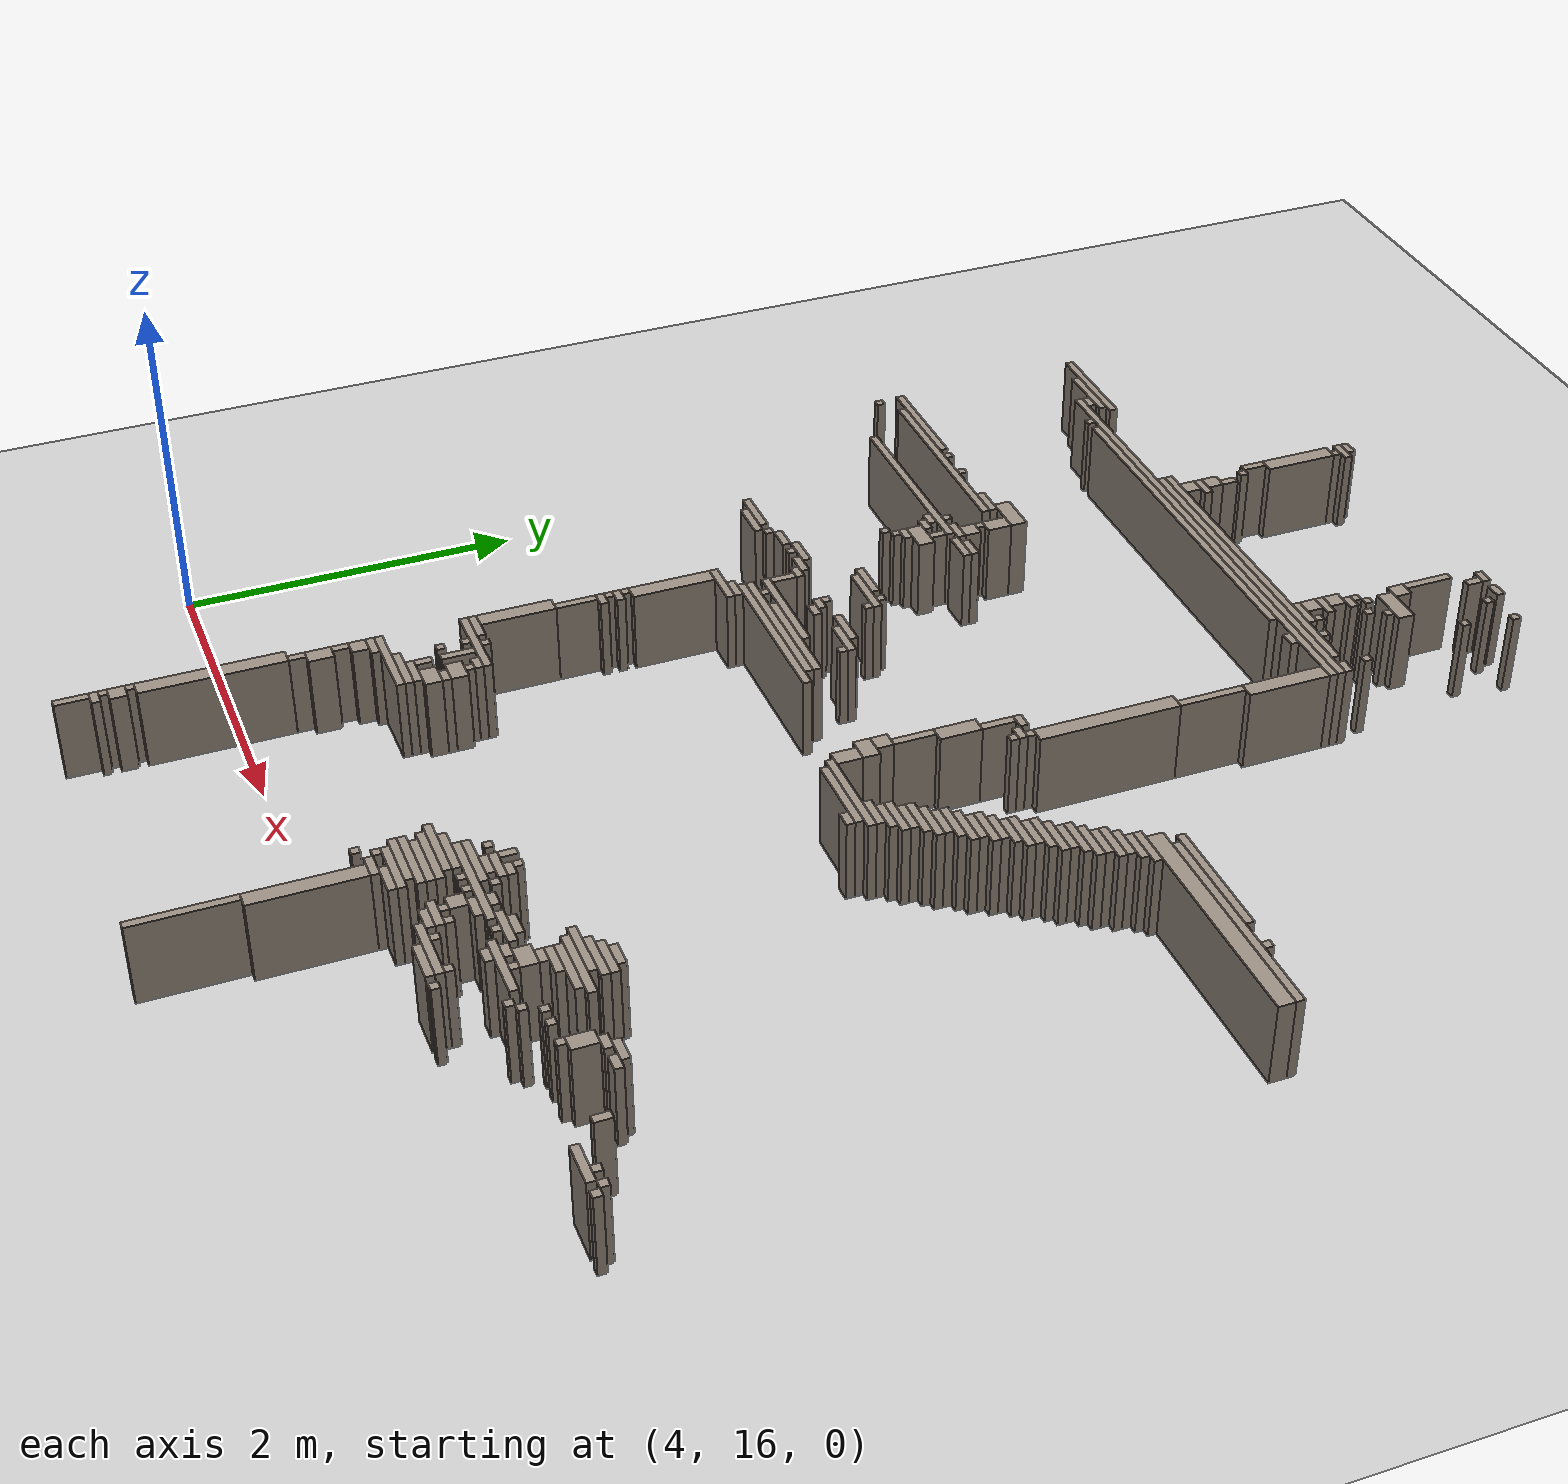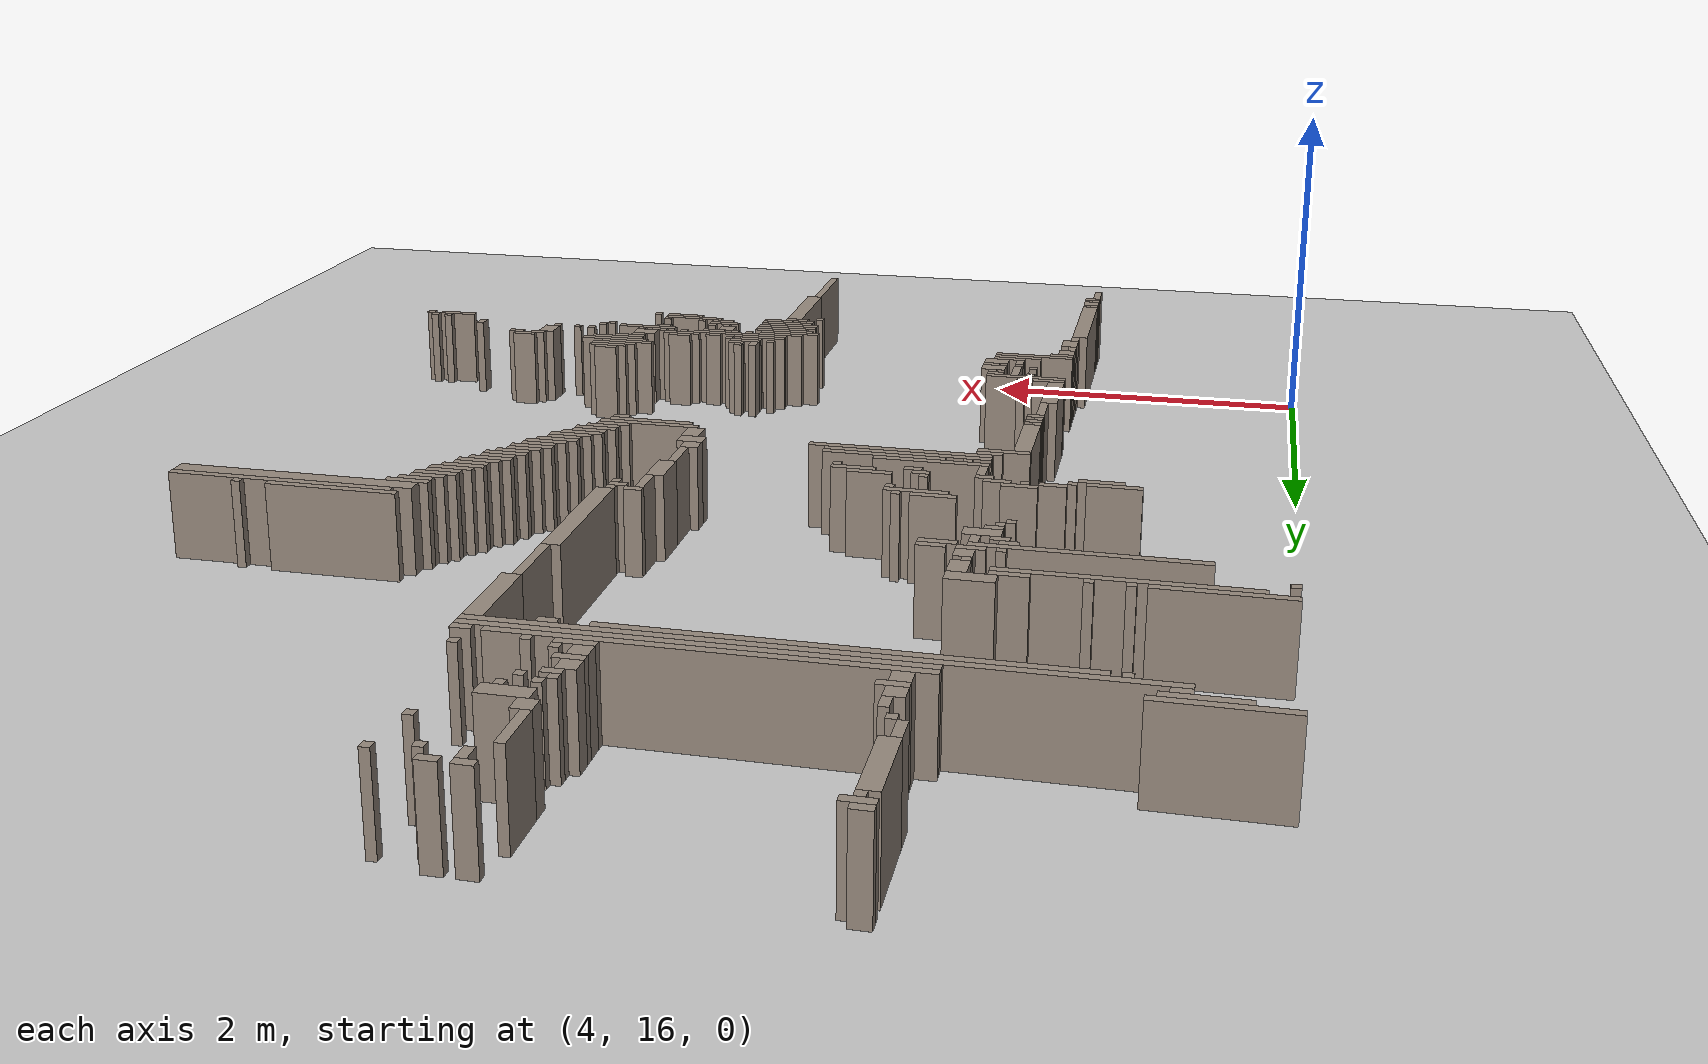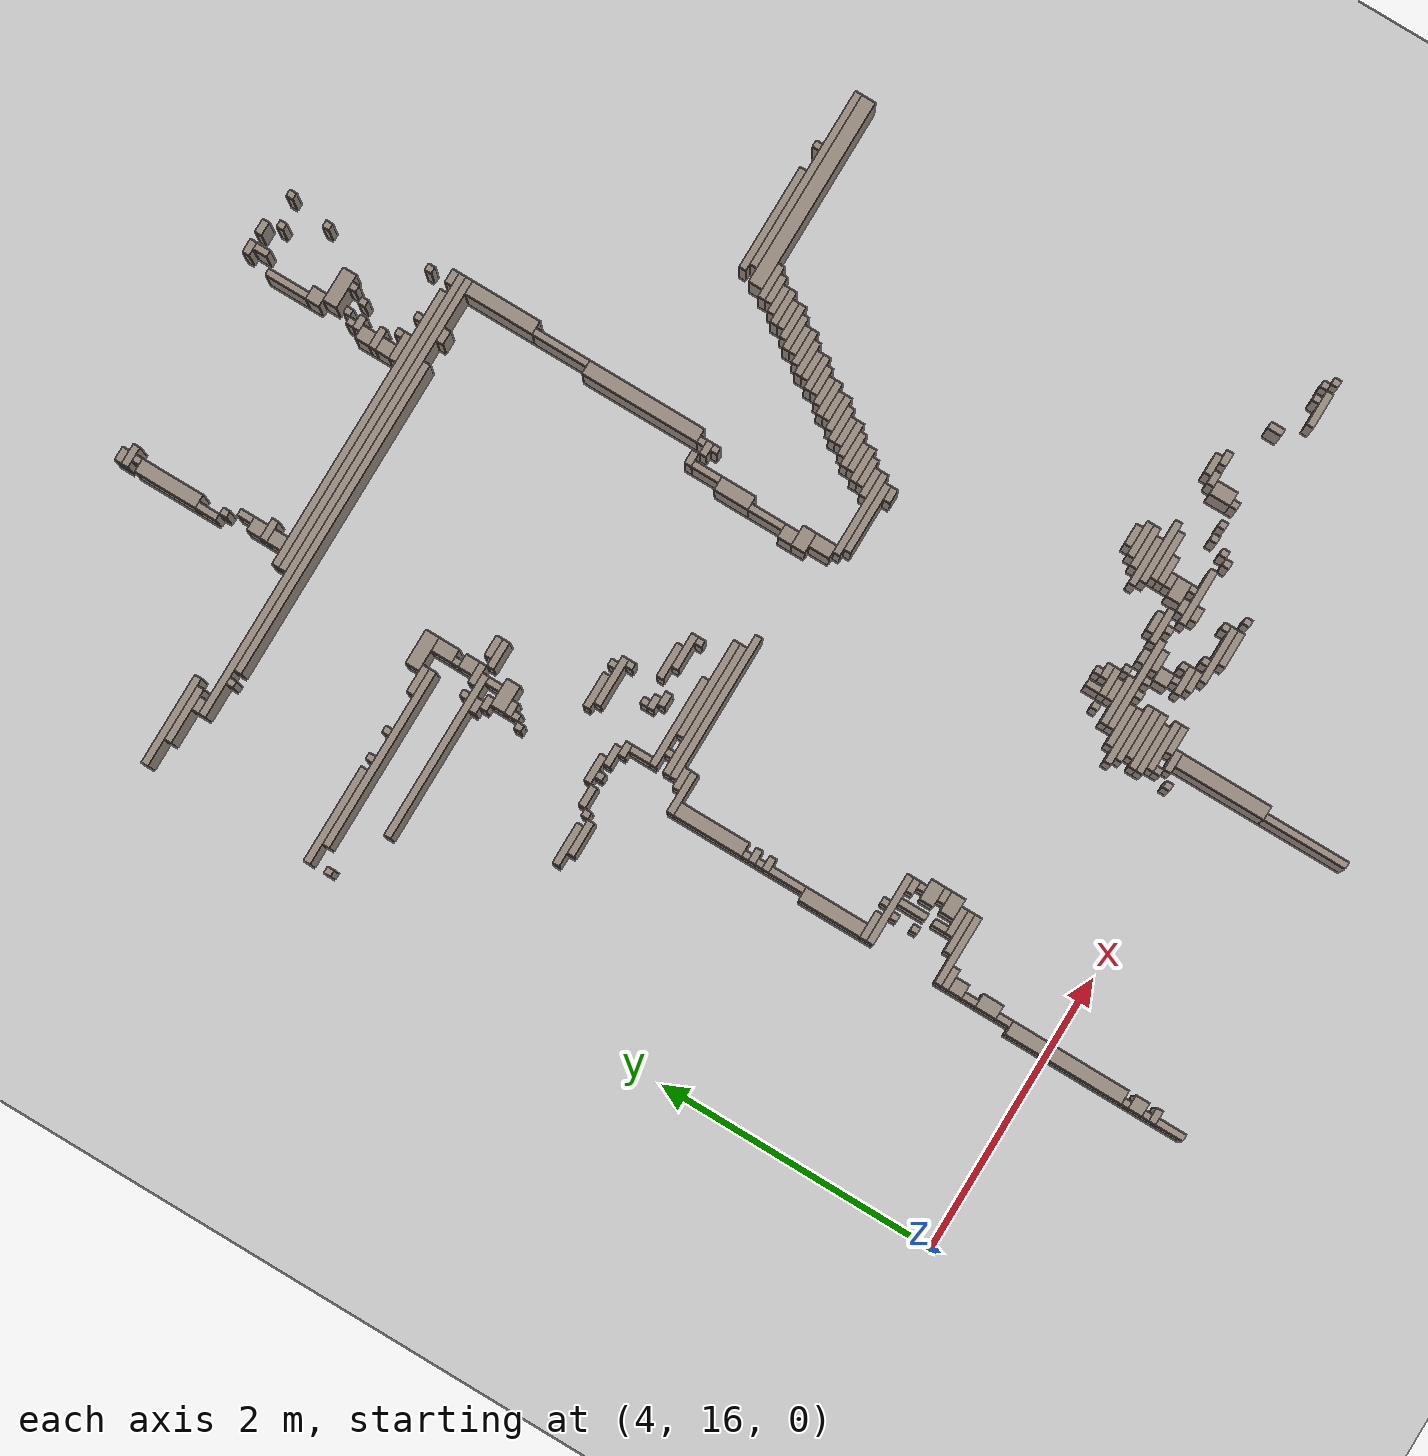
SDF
<?xml version="1.0" ?>
<sdf version="1.8">
  <world name="andar3porta2">
    <physics name="1ms" type="ignored"><max_step_size>0.001</max_step_size><real_time_factor>1.0</real_time_factor></physics>
    <plugin filename="gz-sim-physics-system" name="gz::sim::systems::Physics"/>
    <plugin filename="gz-sim-user-commands-system" name="gz::sim::systems::UserCommands"/>
    <plugin filename="gz-sim-scene-broadcaster-system" name="gz::sim::systems::SceneBroadcaster"/>
    <plugin filename="gz-sim-sensors-system" name="gz::sim::systems::Sensors"><render_engine>ogre2</render_engine></plugin>
    <light type="directional" name="sun">
      <cast_shadows>false</cast_shadows>
      <pose>0 0 10 0 0 0</pose>
      <diffuse>0.9 0.9 0.9 1</diffuse>
      <direction>-0.3 0.2 -0.9</direction>
    </light>
    <model name="ground_plane">
      <static>true</static>
      <link name="link">
        <collision name="col"><geometry><plane><normal>0 0 1</normal><size>100 100</size></plane></geometry></collision>
        <visual name="vis"><geometry><plane><normal>0 0 1</normal><size>100 100</size></plane></geometry>
          <material><ambient>0.8 0.8 0.8 1</ambient><diffuse>0.8 0.8 0.8 1</diffuse></material></visual>
      </link>
    </model>

    <model name="walls">
      <static>true</static>
      <link name="link">
        <collision name="c0"><pose>5.639 22.983 0.250 0 0 0</pose><geometry><box><size>0.100 0.050 0.500</size></box></geometry></collision><visual name="v0"><pose>5.639 22.983 0.250 0 0 0</pose><geometry><box><size>0.100 0.050 0.500</size></box></geometry><material><ambient>0.6 0.55 0.5 1</ambient><diffuse>0.6 0.55 0.5 1</diffuse></material></visual>
        <collision name="c1"><pose>5.664 22.883 0.250 0 0 0</pose><geometry><box><size>0.050 0.050 0.500</size></box></geometry></collision><visual name="v1"><pose>5.664 22.883 0.250 0 0 0</pose><geometry><box><size>0.050 0.050 0.500</size></box></geometry><material><ambient>0.6 0.55 0.5 1</ambient><diffuse>0.6 0.55 0.5 1</diffuse></material></visual>
        <collision name="c2"><pose>7.114 22.658 0.250 0 0 0</pose><geometry><box><size>0.050 0.300 0.500</size></box></geometry></collision><visual name="v2"><pose>7.114 22.658 0.250 0 0 0</pose><geometry><box><size>0.050 0.300 0.500</size></box></geometry><material><ambient>0.6 0.55 0.5 1</ambient><diffuse>0.6 0.55 0.5 1</diffuse></material></visual>
        <collision name="c3"><pose>7.139 22.458 0.250 0 0 0</pose><geometry><box><size>0.100 0.100 0.500</size></box></geometry></collision><visual name="v3"><pose>7.139 22.458 0.250 0 0 0</pose><geometry><box><size>0.100 0.100 0.500</size></box></geometry><material><ambient>0.6 0.55 0.5 1</ambient><diffuse>0.6 0.55 0.5 1</diffuse></material></visual>
        <collision name="c4"><pose>7.089 22.058 0.250 0 0 0</pose><geometry><box><size>0.100 0.100 0.500</size></box></geometry></collision><visual name="v4"><pose>7.089 22.058 0.250 0 0 0</pose><geometry><box><size>0.100 0.100 0.500</size></box></geometry><material><ambient>0.6 0.55 0.5 1</ambient><diffuse>0.6 0.55 0.5 1</diffuse></material></visual>
        <collision name="c5"><pose>5.689 22.008 0.250 0 0 0</pose><geometry><box><size>0.100 0.100 0.500</size></box></geometry></collision><visual name="v5"><pose>5.689 22.008 0.250 0 0 0</pose><geometry><box><size>0.100 0.100 0.500</size></box></geometry><material><ambient>0.6 0.55 0.5 1</ambient><diffuse>0.6 0.55 0.5 1</diffuse></material></visual>
        <collision name="c6"><pose>7.214 22.908 0.250 0 0 0</pose><geometry><box><size>0.050 0.100 0.500</size></box></geometry></collision><visual name="v6"><pose>7.214 22.908 0.250 0 0 0</pose><geometry><box><size>0.050 0.100 0.500</size></box></geometry><material><ambient>0.6 0.55 0.5 1</ambient><diffuse>0.6 0.55 0.5 1</diffuse></material></visual>
        <collision name="c7"><pose>7.339 22.983 0.250 0 0 0</pose><geometry><box><size>0.100 0.050 0.500</size></box></geometry></collision><visual name="v7"><pose>7.339 22.983 0.250 0 0 0</pose><geometry><box><size>0.100 0.050 0.500</size></box></geometry><material><ambient>0.6 0.55 0.5 1</ambient><diffuse>0.6 0.55 0.5 1</diffuse></material></visual>
        <collision name="c8"><pose>7.689 21.783 0.250 0 0 0</pose><geometry><box><size>0.100 0.050 0.500</size></box></geometry></collision><visual name="v8"><pose>7.689 21.783 0.250 0 0 0</pose><geometry><box><size>0.100 0.050 0.500</size></box></geometry><material><ambient>0.6 0.55 0.5 1</ambient><diffuse>0.6 0.55 0.5 1</diffuse></material></visual>
        <collision name="c9"><pose>7.664 21.933 0.250 0 0 0</pose><geometry><box><size>0.050 0.050 0.500</size></box></geometry></collision><visual name="v9"><pose>7.664 21.933 0.250 0 0 0</pose><geometry><box><size>0.050 0.050 0.500</size></box></geometry><material><ambient>0.6 0.55 0.5 1</ambient><diffuse>0.6 0.55 0.5 1</diffuse></material></visual>
        <collision name="c10"><pose>5.639 22.633 0.250 0 0 0</pose><geometry><box><size>0.100 0.450 0.500</size></box></geometry></collision><visual name="v10"><pose>5.639 22.633 0.250 0 0 0</pose><geometry><box><size>0.100 0.450 0.500</size></box></geometry><material><ambient>0.6 0.55 0.5 1</ambient><diffuse>0.6 0.55 0.5 1</diffuse></material></visual>
        <collision name="c11"><pose>5.614 22.333 0.250 0 0 0</pose><geometry><box><size>0.050 0.150 0.500</size></box></geometry></collision><visual name="v11"><pose>5.614 22.333 0.250 0 0 0</pose><geometry><box><size>0.050 0.150 0.500</size></box></geometry><material><ambient>0.6 0.55 0.5 1</ambient><diffuse>0.6 0.55 0.5 1</diffuse></material></visual>
        <collision name="c12"><pose>5.639 20.583 0.250 0 0 0</pose><geometry><box><size>0.100 0.150 0.500</size></box></geometry></collision><visual name="v12"><pose>5.639 20.583 0.250 0 0 0</pose><geometry><box><size>0.100 0.150 0.500</size></box></geometry><material><ambient>0.6 0.55 0.5 1</ambient><diffuse>0.6 0.55 0.5 1</diffuse></material></visual>
        <collision name="c13"><pose>5.614 20.483 0.250 0 0 0</pose><geometry><box><size>0.050 0.050 0.500</size></box></geometry></collision><visual name="v13"><pose>5.614 20.483 0.250 0 0 0</pose><geometry><box><size>0.050 0.050 0.500</size></box></geometry><material><ambient>0.6 0.55 0.5 1</ambient><diffuse>0.6 0.55 0.5 1</diffuse></material></visual>
        <collision name="c14"><pose>5.464 20.333 0.250 0 0 0</pose><geometry><box><size>0.050 0.050 0.500</size></box></geometry></collision><visual name="v14"><pose>5.464 20.333 0.250 0 0 0</pose><geometry><box><size>0.050 0.050 0.500</size></box></geometry><material><ambient>0.6 0.55 0.5 1</ambient><diffuse>0.6 0.55 0.5 1</diffuse></material></visual>
        <collision name="c15"><pose>7.614 22.933 0.250 0 0 0</pose><geometry><box><size>0.050 0.050 0.500</size></box></geometry></collision><visual name="v15"><pose>7.614 22.933 0.250 0 0 0</pose><geometry><box><size>0.050 0.050 0.500</size></box></geometry><material><ambient>0.6 0.55 0.5 1</ambient><diffuse>0.6 0.55 0.5 1</diffuse></material></visual>
        <collision name="c16"><pose>7.614 19.883 0.250 0 0 0</pose><geometry><box><size>0.050 0.050 0.500</size></box></geometry></collision><visual name="v16"><pose>7.614 19.883 0.250 0 0 0</pose><geometry><box><size>0.050 0.050 0.500</size></box></geometry><material><ambient>0.6 0.55 0.5 1</ambient><diffuse>0.6 0.55 0.5 1</diffuse></material></visual>
        <collision name="c17"><pose>7.414 22.883 0.250 0 0 0</pose><geometry><box><size>0.050 0.050 0.500</size></box></geometry></collision><visual name="v17"><pose>7.414 22.883 0.250 0 0 0</pose><geometry><box><size>0.050 0.050 0.500</size></box></geometry><material><ambient>0.6 0.55 0.5 1</ambient><diffuse>0.6 0.55 0.5 1</diffuse></material></visual>
        <collision name="c18"><pose>5.464 19.933 0.250 0 0 0</pose><geometry><box><size>0.050 0.050 0.500</size></box></geometry></collision><visual name="v18"><pose>5.464 19.933 0.250 0 0 0</pose><geometry><box><size>0.050 0.050 0.500</size></box></geometry><material><ambient>0.6 0.55 0.5 1</ambient><diffuse>0.6 0.55 0.5 1</diffuse></material></visual>
        <collision name="c19"><pose>5.614 20.333 0.250 0 0 0</pose><geometry><box><size>0.150 0.050 0.500</size></box></geometry></collision><visual name="v19"><pose>5.614 20.333 0.250 0 0 0</pose><geometry><box><size>0.150 0.050 0.500</size></box></geometry><material><ambient>0.6 0.55 0.5 1</ambient><diffuse>0.6 0.55 0.5 1</diffuse></material></visual>
        <collision name="c20"><pose>5.689 21.858 0.250 0 0 0</pose><geometry><box><size>0.100 0.100 0.500</size></box></geometry></collision><visual name="v20"><pose>5.689 21.858 0.250 0 0 0</pose><geometry><box><size>0.100 0.100 0.500</size></box></geometry><material><ambient>0.6 0.55 0.5 1</ambient><diffuse>0.6 0.55 0.5 1</diffuse></material></visual>
        <collision name="c21"><pose>5.714 22.108 0.250 0 0 0</pose><geometry><box><size>0.050 0.100 0.500</size></box></geometry></collision><visual name="v21"><pose>5.714 22.108 0.250 0 0 0</pose><geometry><box><size>0.050 0.100 0.500</size></box></geometry><material><ambient>0.6 0.55 0.5 1</ambient><diffuse>0.6 0.55 0.5 1</diffuse></material></visual>
        <collision name="c22"><pose>7.439 19.533 0.250 0 0 0</pose><geometry><box><size>0.100 0.250 0.500</size></box></geometry></collision><visual name="v22"><pose>7.439 19.533 0.250 0 0 0</pose><geometry><box><size>0.100 0.250 0.500</size></box></geometry><material><ambient>0.6 0.55 0.5 1</ambient><diffuse>0.6 0.55 0.5 1</diffuse></material></visual>
        <collision name="c23"><pose>5.714 21.933 0.250 0 0 0</pose><geometry><box><size>0.150 0.050 0.500</size></box></geometry></collision><visual name="v23"><pose>5.714 21.933 0.250 0 0 0</pose><geometry><box><size>0.150 0.050 0.500</size></box></geometry><material><ambient>0.6 0.55 0.5 1</ambient><diffuse>0.6 0.55 0.5 1</diffuse></material></visual>
        <collision name="c24"><pose>5.539 20.033 0.250 0 0 0</pose><geometry><box><size>0.100 0.050 0.500</size></box></geometry></collision><visual name="v24"><pose>5.539 20.033 0.250 0 0 0</pose><geometry><box><size>0.100 0.050 0.500</size></box></geometry><material><ambient>0.6 0.55 0.5 1</ambient><diffuse>0.6 0.55 0.5 1</diffuse></material></visual>
        <collision name="c25"><pose>5.514 19.983 0.250 0 0 0</pose><geometry><box><size>0.050 0.050 0.500</size></box></geometry></collision><visual name="v25"><pose>5.514 19.983 0.250 0 0 0</pose><geometry><box><size>0.050 0.050 0.500</size></box></geometry><material><ambient>0.6 0.55 0.5 1</ambient><diffuse>0.6 0.55 0.5 1</diffuse></material></visual>
        <collision name="c26"><pose>5.539 18.558 0.250 0 0 0</pose><geometry><box><size>0.100 0.500 0.500</size></box></geometry></collision><visual name="v26"><pose>5.539 18.558 0.250 0 0 0</pose><geometry><box><size>0.100 0.500 0.500</size></box></geometry><material><ambient>0.6 0.55 0.5 1</ambient><diffuse>0.6 0.55 0.5 1</diffuse></material></visual>
        <collision name="c27"><pose>5.514 18.283 0.250 0 0 0</pose><geometry><box><size>0.050 0.050 0.500</size></box></geometry></collision><visual name="v27"><pose>5.514 18.283 0.250 0 0 0</pose><geometry><box><size>0.050 0.050 0.500</size></box></geometry><material><ambient>0.6 0.55 0.5 1</ambient><diffuse>0.6 0.55 0.5 1</diffuse></material></visual>
        <collision name="c28"><pose>5.539 18.233 0.250 0 0 0</pose><geometry><box><size>0.100 0.050 0.500</size></box></geometry></collision><visual name="v28"><pose>5.539 18.233 0.250 0 0 0</pose><geometry><box><size>0.100 0.050 0.500</size></box></geometry><material><ambient>0.6 0.55 0.5 1</ambient><diffuse>0.6 0.55 0.5 1</diffuse></material></visual>
        <collision name="c29"><pose>5.514 18.183 0.250 0 0 0</pose><geometry><box><size>0.050 0.050 0.500</size></box></geometry></collision><visual name="v29"><pose>5.514 18.183 0.250 0 0 0</pose><geometry><box><size>0.050 0.050 0.500</size></box></geometry><material><ambient>0.6 0.55 0.5 1</ambient><diffuse>0.6 0.55 0.5 1</diffuse></material></visual>
        <collision name="c30"><pose>5.489 20.183 0.250 0 0 0</pose><geometry><box><size>0.100 0.050 0.500</size></box></geometry></collision><visual name="v30"><pose>5.489 20.183 0.250 0 0 0</pose><geometry><box><size>0.100 0.050 0.500</size></box></geometry><material><ambient>0.6 0.55 0.5 1</ambient><diffuse>0.6 0.55 0.5 1</diffuse></material></visual>
        <collision name="c31"><pose>5.714 19.183 0.250 0 0 0</pose><geometry><box><size>0.050 0.150 0.500</size></box></geometry></collision><visual name="v31"><pose>5.714 19.183 0.250 0 0 0</pose><geometry><box><size>0.050 0.150 0.500</size></box></geometry><material><ambient>0.6 0.55 0.5 1</ambient><diffuse>0.6 0.55 0.5 1</diffuse></material></visual>
        <collision name="c32"><pose>5.664 22.233 0.250 0 0 0</pose><geometry><box><size>0.050 0.050 0.500</size></box></geometry></collision><visual name="v32"><pose>5.664 22.233 0.250 0 0 0</pose><geometry><box><size>0.050 0.050 0.500</size></box></geometry><material><ambient>0.6 0.55 0.5 1</ambient><diffuse>0.6 0.55 0.5 1</diffuse></material></visual>
        <collision name="c33"><pose>8.514 19.733 0.250 0 0 0</pose><geometry><box><size>0.250 0.050 0.500</size></box></geometry></collision><visual name="v33"><pose>8.514 19.733 0.250 0 0 0</pose><geometry><box><size>0.250 0.050 0.500</size></box></geometry><material><ambient>0.6 0.55 0.5 1</ambient><diffuse>0.6 0.55 0.5 1</diffuse></material></visual>
        <collision name="c34"><pose>5.664 17.283 0.250 0 0 0</pose><geometry><box><size>0.050 0.050 0.500</size></box></geometry></collision><visual name="v34"><pose>5.664 17.283 0.250 0 0 0</pose><geometry><box><size>0.050 0.050 0.500</size></box></geometry><material><ambient>0.6 0.55 0.5 1</ambient><diffuse>0.6 0.55 0.5 1</diffuse></material></visual>
        <collision name="c35"><pose>5.764 17.208 0.250 0 0 0</pose><geometry><box><size>0.050 0.200 0.500</size></box></geometry></collision><visual name="v35"><pose>5.764 17.208 0.250 0 0 0</pose><geometry><box><size>0.050 0.200 0.500</size></box></geometry><material><ambient>0.6 0.55 0.5 1</ambient><diffuse>0.6 0.55 0.5 1</diffuse></material></visual>
        <collision name="c36"><pose>5.914 17.158 0.250 0 0 0</pose><geometry><box><size>0.150 0.100 0.500</size></box></geometry></collision><visual name="v36"><pose>5.914 17.158 0.250 0 0 0</pose><geometry><box><size>0.150 0.100 0.500</size></box></geometry><material><ambient>0.6 0.55 0.5 1</ambient><diffuse>0.6 0.55 0.5 1</diffuse></material></visual>
        <collision name="c37"><pose>7.564 22.633 0.250 0 0 0</pose><geometry><box><size>0.050 0.050 0.500</size></box></geometry></collision><visual name="v37"><pose>7.564 22.633 0.250 0 0 0</pose><geometry><box><size>0.050 0.050 0.500</size></box></geometry><material><ambient>0.6 0.55 0.5 1</ambient><diffuse>0.6 0.55 0.5 1</diffuse></material></visual>
        <collision name="c38"><pose>7.664 20.958 0.250 0 0 0</pose><geometry><box><size>0.050 0.400 0.500</size></box></geometry></collision><visual name="v38"><pose>7.664 20.958 0.250 0 0 0</pose><geometry><box><size>0.050 0.400 0.500</size></box></geometry><material><ambient>0.6 0.55 0.5 1</ambient><diffuse>0.6 0.55 0.5 1</diffuse></material></visual>
        <collision name="c39"><pose>7.689 21.408 0.250 0 0 0</pose><geometry><box><size>0.100 0.500 0.500</size></box></geometry></collision><visual name="v39"><pose>7.689 21.408 0.250 0 0 0</pose><geometry><box><size>0.100 0.500 0.500</size></box></geometry><material><ambient>0.6 0.55 0.5 1</ambient><diffuse>0.6 0.55 0.5 1</diffuse></material></visual>
        <collision name="c40"><pose>7.464 19.758 0.250 0 0 0</pose><geometry><box><size>0.050 0.200 0.500</size></box></geometry></collision><visual name="v40"><pose>7.464 19.758 0.250 0 0 0</pose><geometry><box><size>0.050 0.200 0.500</size></box></geometry><material><ambient>0.6 0.55 0.5 1</ambient><diffuse>0.6 0.55 0.5 1</diffuse></material></visual>
        <collision name="c41"><pose>5.689 17.333 0.250 0 0 0</pose><geometry><box><size>0.500 0.050 0.500</size></box></geometry></collision><visual name="v41"><pose>5.689 17.333 0.250 0 0 0</pose><geometry><box><size>0.500 0.050 0.500</size></box></geometry><material><ambient>0.6 0.55 0.5 1</ambient><diffuse>0.6 0.55 0.5 1</diffuse></material></visual>
        <collision name="c42"><pose>8.114 19.083 0.250 0 0 0</pose><geometry><box><size>0.250 0.050 0.500</size></box></geometry></collision><visual name="v42"><pose>8.114 19.083 0.250 0 0 0</pose><geometry><box><size>0.250 0.050 0.500</size></box></geometry><material><ambient>0.6 0.55 0.5 1</ambient><diffuse>0.6 0.55 0.5 1</diffuse></material></visual>
        <collision name="c43"><pose>5.489 17.633 0.250 0 0 0</pose><geometry><box><size>0.100 0.450 0.500</size></box></geometry></collision><visual name="v43"><pose>5.489 17.633 0.250 0 0 0</pose><geometry><box><size>0.100 0.450 0.500</size></box></geometry><material><ambient>0.6 0.55 0.5 1</ambient><diffuse>0.6 0.55 0.5 1</diffuse></material></visual>
        <collision name="c44"><pose>7.664 16.983 0.250 0 0 0</pose><geometry><box><size>0.050 0.050 0.500</size></box></geometry></collision><visual name="v44"><pose>7.664 16.983 0.250 0 0 0</pose><geometry><box><size>0.050 0.050 0.500</size></box></geometry><material><ambient>0.6 0.55 0.5 1</ambient><diffuse>0.6 0.55 0.5 1</diffuse></material></visual>
        <collision name="c45"><pose>7.764 16.833 0.250 0 0 0</pose><geometry><box><size>0.050 0.050 0.500</size></box></geometry></collision><visual name="v45"><pose>7.764 16.833 0.250 0 0 0</pose><geometry><box><size>0.050 0.050 0.500</size></box></geometry><material><ambient>0.6 0.55 0.5 1</ambient><diffuse>0.6 0.55 0.5 1</diffuse></material></visual>
        <collision name="c46"><pose>5.464 19.333 0.250 0 0 0</pose><geometry><box><size>0.050 0.050 0.500</size></box></geometry></collision><visual name="v46"><pose>5.464 19.333 0.250 0 0 0</pose><geometry><box><size>0.050 0.050 0.500</size></box></geometry><material><ambient>0.6 0.55 0.5 1</ambient><diffuse>0.6 0.55 0.5 1</diffuse></material></visual>
        <collision name="c47"><pose>8.289 16.733 0.250 0 0 0</pose><geometry><box><size>0.100 0.050 0.500</size></box></geometry></collision><visual name="v47"><pose>8.289 16.733 0.250 0 0 0</pose><geometry><box><size>0.100 0.050 0.500</size></box></geometry><material><ambient>0.6 0.55 0.5 1</ambient><diffuse>0.6 0.55 0.5 1</diffuse></material></visual>
        <collision name="c48"><pose>5.489 16.708 0.250 0 0 0</pose><geometry><box><size>0.100 0.100 0.500</size></box></geometry></collision><visual name="v48"><pose>5.489 16.708 0.250 0 0 0</pose><geometry><box><size>0.100 0.100 0.500</size></box></geometry><material><ambient>0.6 0.55 0.5 1</ambient><diffuse>0.6 0.55 0.5 1</diffuse></material></visual>
        <collision name="c49"><pose>7.439 16.583 0.250 0 0 0</pose><geometry><box><size>0.400 0.050 0.500</size></box></geometry></collision><visual name="v49"><pose>7.439 16.583 0.250 0 0 0</pose><geometry><box><size>0.400 0.050 0.500</size></box></geometry><material><ambient>0.6 0.55 0.5 1</ambient><diffuse>0.6 0.55 0.5 1</diffuse></material></visual>
        <collision name="c50"><pose>7.914 16.683 0.250 0 0 0</pose><geometry><box><size>0.150 0.050 0.500</size></box></geometry></collision><visual name="v50"><pose>7.914 16.683 0.250 0 0 0</pose><geometry><box><size>0.150 0.050 0.500</size></box></geometry><material><ambient>0.6 0.55 0.5 1</ambient><diffuse>0.6 0.55 0.5 1</diffuse></material></visual>
        <collision name="c51"><pose>5.464 16.608 0.250 0 0 0</pose><geometry><box><size>0.050 0.100 0.500</size></box></geometry></collision><visual name="v51"><pose>5.464 16.608 0.250 0 0 0</pose><geometry><box><size>0.050 0.100 0.500</size></box></geometry><material><ambient>0.6 0.55 0.5 1</ambient><diffuse>0.6 0.55 0.5 1</diffuse></material></visual>
        <collision name="c52"><pose>7.464 16.533 0.250 0 0 0</pose><geometry><box><size>0.350 0.050 0.500</size></box></geometry></collision><visual name="v52"><pose>7.464 16.533 0.250 0 0 0</pose><geometry><box><size>0.350 0.050 0.500</size></box></geometry><material><ambient>0.6 0.55 0.5 1</ambient><diffuse>0.6 0.55 0.5 1</diffuse></material></visual>
        <collision name="c53"><pose>7.314 22.283 0.250 0 0 0</pose><geometry><box><size>0.050 0.050 0.500</size></box></geometry></collision><visual name="v53"><pose>7.314 22.283 0.250 0 0 0</pose><geometry><box><size>0.050 0.050 0.500</size></box></geometry><material><ambient>0.6 0.55 0.5 1</ambient><diffuse>0.6 0.55 0.5 1</diffuse></material></visual>
        <collision name="c54"><pose>8.214 19.233 0.250 0 0 0</pose><geometry><box><size>0.250 0.050 0.500</size></box></geometry></collision><visual name="v54"><pose>8.214 19.233 0.250 0 0 0</pose><geometry><box><size>0.250 0.050 0.500</size></box></geometry><material><ambient>0.6 0.55 0.5 1</ambient><diffuse>0.6 0.55 0.5 1</diffuse></material></visual>
        <collision name="c55"><pose>8.414 16.733 0.250 0 0 0</pose><geometry><box><size>0.050 0.050 0.500</size></box></geometry></collision><visual name="v55"><pose>8.414 16.733 0.250 0 0 0</pose><geometry><box><size>0.050 0.050 0.500</size></box></geometry><material><ambient>0.6 0.55 0.5 1</ambient><diffuse>0.6 0.55 0.5 1</diffuse></material></visual>
        <collision name="c56"><pose>5.439 20.233 0.250 0 0 0</pose><geometry><box><size>0.100 0.050 0.500</size></box></geometry></collision><visual name="v56"><pose>5.439 20.233 0.250 0 0 0</pose><geometry><box><size>0.100 0.050 0.500</size></box></geometry><material><ambient>0.6 0.55 0.5 1</ambient><diffuse>0.6 0.55 0.5 1</diffuse></material></visual>
        <collision name="c57"><pose>7.414 19.008 0.250 0 0 0</pose><geometry><box><size>0.150 0.100 0.500</size></box></geometry></collision><visual name="v57"><pose>7.414 19.008 0.250 0 0 0</pose><geometry><box><size>0.150 0.100 0.500</size></box></geometry><material><ambient>0.6 0.55 0.5 1</ambient><diffuse>0.6 0.55 0.5 1</diffuse></material></visual>
        <collision name="c58"><pose>7.264 22.183 0.250 0 0 0</pose><geometry><box><size>0.050 0.050 0.500</size></box></geometry></collision><visual name="v58"><pose>7.264 22.183 0.250 0 0 0</pose><geometry><box><size>0.050 0.050 0.500</size></box></geometry><material><ambient>0.6 0.55 0.5 1</ambient><diffuse>0.6 0.55 0.5 1</diffuse></material></visual>
        <collision name="c59"><pose>7.439 18.883 0.250 0 0 0</pose><geometry><box><size>0.100 0.150 0.500</size></box></geometry></collision><visual name="v59"><pose>7.439 18.883 0.250 0 0 0</pose><geometry><box><size>0.100 0.150 0.500</size></box></geometry><material><ambient>0.6 0.55 0.5 1</ambient><diffuse>0.6 0.55 0.5 1</diffuse></material></visual>
        <collision name="c60"><pose>7.414 19.283 0.250 0 0 0</pose><geometry><box><size>0.050 0.250 0.500</size></box></geometry></collision><visual name="v60"><pose>7.414 19.283 0.250 0 0 0</pose><geometry><box><size>0.050 0.250 0.500</size></box></geometry><material><ambient>0.6 0.55 0.5 1</ambient><diffuse>0.6 0.55 0.5 1</diffuse></material></visual>
        <collision name="c61"><pose>5.439 15.883 0.250 0 0 0</pose><geometry><box><size>0.100 0.850 0.500</size></box></geometry></collision><visual name="v61"><pose>5.439 15.883 0.250 0 0 0</pose><geometry><box><size>0.100 0.850 0.500</size></box></geometry><material><ambient>0.6 0.55 0.5 1</ambient><diffuse>0.6 0.55 0.5 1</diffuse></material></visual>
        <collision name="c62"><pose>5.414 15.433 0.250 0 0 0</pose><geometry><box><size>0.050 0.050 0.500</size></box></geometry></collision><visual name="v62"><pose>5.414 15.433 0.250 0 0 0</pose><geometry><box><size>0.050 0.050 0.500</size></box></geometry><material><ambient>0.6 0.55 0.5 1</ambient><diffuse>0.6 0.55 0.5 1</diffuse></material></visual>
        <collision name="c63"><pose>5.439 15.358 0.250 0 0 0</pose><geometry><box><size>0.100 0.100 0.500</size></box></geometry></collision><visual name="v63"><pose>5.439 15.358 0.250 0 0 0</pose><geometry><box><size>0.100 0.100 0.500</size></box></geometry><material><ambient>0.6 0.55 0.5 1</ambient><diffuse>0.6 0.55 0.5 1</diffuse></material></visual>
        <collision name="c64"><pose>5.414 15.283 0.250 0 0 0</pose><geometry><box><size>0.050 0.050 0.500</size></box></geometry></collision><visual name="v64"><pose>5.414 15.283 0.250 0 0 0</pose><geometry><box><size>0.050 0.050 0.500</size></box></geometry><material><ambient>0.6 0.55 0.5 1</ambient><diffuse>0.6 0.55 0.5 1</diffuse></material></visual>
        <collision name="c65"><pose>5.639 20.408 0.250 0 0 0</pose><geometry><box><size>0.100 0.100 0.500</size></box></geometry></collision><visual name="v65"><pose>5.639 20.408 0.250 0 0 0</pose><geometry><box><size>0.100 0.100 0.500</size></box></geometry><material><ambient>0.6 0.55 0.5 1</ambient><diffuse>0.6 0.55 0.5 1</diffuse></material></visual>
        <collision name="c66"><pose>7.189 22.983 0.250 0 0 0</pose><geometry><box><size>0.100 0.050 0.500</size></box></geometry></collision><visual name="v66"><pose>7.189 22.983 0.250 0 0 0</pose><geometry><box><size>0.100 0.050 0.500</size></box></geometry><material><ambient>0.6 0.55 0.5 1</ambient><diffuse>0.6 0.55 0.5 1</diffuse></material></visual>
        <collision name="c67"><pose>7.339 21.633 0.250 0 0 0</pose><geometry><box><size>0.100 0.050 0.500</size></box></geometry></collision><visual name="v67"><pose>7.339 21.633 0.250 0 0 0</pose><geometry><box><size>0.100 0.050 0.500</size></box></geometry><material><ambient>0.6 0.55 0.5 1</ambient><diffuse>0.6 0.55 0.5 1</diffuse></material></visual>
        <collision name="c68"><pose>5.664 22.933 0.250 0 0 0</pose><geometry><box><size>0.150 0.050 0.500</size></box></geometry></collision><visual name="v68"><pose>5.664 22.933 0.250 0 0 0</pose><geometry><box><size>0.150 0.050 0.500</size></box></geometry><material><ambient>0.6 0.55 0.5 1</ambient><diffuse>0.6 0.55 0.5 1</diffuse></material></visual>
        <collision name="c69"><pose>7.214 21.883 0.250 0 0 0</pose><geometry><box><size>0.050 0.050 0.500</size></box></geometry></collision><visual name="v69"><pose>7.214 21.883 0.250 0 0 0</pose><geometry><box><size>0.050 0.050 0.500</size></box></geometry><material><ambient>0.6 0.55 0.5 1</ambient><diffuse>0.6 0.55 0.5 1</diffuse></material></visual>
        <collision name="c70"><pose>7.614 19.783 0.250 0 0 0</pose><geometry><box><size>0.050 0.050 0.500</size></box></geometry></collision><visual name="v70"><pose>7.614 19.783 0.250 0 0 0</pose><geometry><box><size>0.050 0.050 0.500</size></box></geometry><material><ambient>0.6 0.55 0.5 1</ambient><diffuse>0.6 0.55 0.5 1</diffuse></material></visual>
        <collision name="c71"><pose>5.664 17.133 0.250 0 0 0</pose><geometry><box><size>0.050 0.050 0.500</size></box></geometry></collision><visual name="v71"><pose>5.664 17.133 0.250 0 0 0</pose><geometry><box><size>0.050 0.050 0.500</size></box></geometry><material><ambient>0.6 0.55 0.5 1</ambient><diffuse>0.6 0.55 0.5 1</diffuse></material></visual>
        <collision name="c72"><pose>7.414 15.308 0.250 0 0 0</pose><geometry><box><size>0.050 0.600 0.500</size></box></geometry></collision><visual name="v72"><pose>7.414 15.308 0.250 0 0 0</pose><geometry><box><size>0.050 0.600 0.500</size></box></geometry><material><ambient>0.6 0.55 0.5 1</ambient><diffuse>0.6 0.55 0.5 1</diffuse></material></visual>
        <collision name="c73"><pose>7.114 22.183 0.250 0 0 0</pose><geometry><box><size>0.050 0.050 0.500</size></box></geometry></collision><visual name="v73"><pose>7.114 22.183 0.250 0 0 0</pose><geometry><box><size>0.050 0.050 0.500</size></box></geometry><material><ambient>0.6 0.55 0.5 1</ambient><diffuse>0.6 0.55 0.5 1</diffuse></material></visual>
        <collision name="c74"><pose>7.564 16.958 0.250 0 0 0</pose><geometry><box><size>0.050 0.100 0.500</size></box></geometry></collision><visual name="v74"><pose>7.564 16.958 0.250 0 0 0</pose><geometry><box><size>0.050 0.100 0.500</size></box></geometry><material><ambient>0.6 0.55 0.5 1</ambient><diffuse>0.6 0.55 0.5 1</diffuse></material></visual>
        <collision name="c75"><pose>7.139 22.133 0.250 0 0 0</pose><geometry><box><size>0.100 0.050 0.500</size></box></geometry></collision><visual name="v75"><pose>7.139 22.133 0.250 0 0 0</pose><geometry><box><size>0.100 0.050 0.500</size></box></geometry><material><ambient>0.6 0.55 0.5 1</ambient><diffuse>0.6 0.55 0.5 1</diffuse></material></visual>
        <collision name="c76"><pose>5.614 20.208 0.250 0 0 0</pose><geometry><box><size>0.050 0.100 0.500</size></box></geometry></collision><visual name="v76"><pose>5.614 20.208 0.250 0 0 0</pose><geometry><box><size>0.050 0.100 0.500</size></box></geometry><material><ambient>0.6 0.55 0.5 1</ambient><diffuse>0.6 0.55 0.5 1</diffuse></material></visual>
        <collision name="c77"><pose>7.264 22.358 0.250 0 0 0</pose><geometry><box><size>0.250 0.100 0.500</size></box></geometry></collision><visual name="v77"><pose>7.264 22.358 0.250 0 0 0</pose><geometry><box><size>0.250 0.100 0.500</size></box></geometry><material><ambient>0.6 0.55 0.5 1</ambient><diffuse>0.6 0.55 0.5 1</diffuse></material></visual>
        <collision name="c78"><pose>7.314 16.333 0.250 0 0 0</pose><geometry><box><size>0.050 0.050 0.500</size></box></geometry></collision><visual name="v78"><pose>7.314 16.333 0.250 0 0 0</pose><geometry><box><size>0.050 0.050 0.500</size></box></geometry><material><ambient>0.6 0.55 0.5 1</ambient><diffuse>0.6 0.55 0.5 1</diffuse></material></visual>
        <collision name="c79"><pose>7.164 22.233 0.250 0 0 0</pose><geometry><box><size>0.050 0.050 0.500</size></box></geometry></collision><visual name="v79"><pose>7.164 22.233 0.250 0 0 0</pose><geometry><box><size>0.050 0.050 0.500</size></box></geometry><material><ambient>0.6 0.55 0.5 1</ambient><diffuse>0.6 0.55 0.5 1</diffuse></material></visual>
        <collision name="c80"><pose>7.264 16.233 0.250 0 0 0</pose><geometry><box><size>0.050 0.050 0.500</size></box></geometry></collision><visual name="v80"><pose>7.264 16.233 0.250 0 0 0</pose><geometry><box><size>0.050 0.050 0.500</size></box></geometry><material><ambient>0.6 0.55 0.5 1</ambient><diffuse>0.6 0.55 0.5 1</diffuse></material></visual>
        <collision name="c81"><pose>5.714 17.383 0.250 0 0 0</pose><geometry><box><size>0.050 0.050 0.500</size></box></geometry></collision><visual name="v81"><pose>5.714 17.383 0.250 0 0 0</pose><geometry><box><size>0.050 0.050 0.500</size></box></geometry><material><ambient>0.6 0.55 0.5 1</ambient><diffuse>0.6 0.55 0.5 1</diffuse></material></visual>
        <collision name="c82"><pose>7.089 21.908 0.250 0 0 0</pose><geometry><box><size>0.100 0.100 0.500</size></box></geometry></collision><visual name="v82"><pose>7.089 21.908 0.250 0 0 0</pose><geometry><box><size>0.100 0.100 0.500</size></box></geometry><material><ambient>0.6 0.55 0.5 1</ambient><diffuse>0.6 0.55 0.5 1</diffuse></material></visual>
        <collision name="c83"><pose>5.689 19.283 0.250 0 0 0</pose><geometry><box><size>0.100 0.050 0.500</size></box></geometry></collision><visual name="v83"><pose>5.689 19.283 0.250 0 0 0</pose><geometry><box><size>0.100 0.050 0.500</size></box></geometry><material><ambient>0.6 0.55 0.5 1</ambient><diffuse>0.6 0.55 0.5 1</diffuse></material></visual>
        <collision name="c84"><pose>7.114 21.983 0.250 0 0 0</pose><geometry><box><size>0.150 0.050 0.500</size></box></geometry></collision><visual name="v84"><pose>7.114 21.983 0.250 0 0 0</pose><geometry><box><size>0.150 0.050 0.500</size></box></geometry><material><ambient>0.6 0.55 0.5 1</ambient><diffuse>0.6 0.55 0.5 1</diffuse></material></visual>
        <collision name="c85"><pose>5.714 18.883 0.250 0 0 0</pose><geometry><box><size>0.150 0.050 0.500</size></box></geometry></collision><visual name="v85"><pose>5.714 18.883 0.250 0 0 0</pose><geometry><box><size>0.150 0.050 0.500</size></box></geometry><material><ambient>0.6 0.55 0.5 1</ambient><diffuse>0.6 0.55 0.5 1</diffuse></material></visual>
        <collision name="c86"><pose>7.664 16.683 0.250 0 0 0</pose><geometry><box><size>0.050 0.050 0.500</size></box></geometry></collision><visual name="v86"><pose>7.664 16.683 0.250 0 0 0</pose><geometry><box><size>0.050 0.050 0.500</size></box></geometry><material><ambient>0.6 0.55 0.5 1</ambient><diffuse>0.6 0.55 0.5 1</diffuse></material></visual>
        <collision name="c87"><pose>4.364 21.833 0.250 0 0 0</pose><geometry><box><size>0.650 0.050 0.500</size></box></geometry></collision><visual name="v87"><pose>4.364 21.833 0.250 0 0 0</pose><geometry><box><size>0.650 0.050 0.500</size></box></geometry><material><ambient>0.6 0.55 0.5 1</ambient><diffuse>0.6 0.55 0.5 1</diffuse></material></visual>
        <collision name="c88"><pose>7.139 21.833 0.250 0 0 0</pose><geometry><box><size>0.200 0.050 0.500</size></box></geometry></collision><visual name="v88"><pose>7.139 21.833 0.250 0 0 0</pose><geometry><box><size>0.200 0.050 0.500</size></box></geometry><material><ambient>0.6 0.55 0.5 1</ambient><diffuse>0.6 0.55 0.5 1</diffuse></material></visual>
        <collision name="c89"><pose>7.364 21.833 0.250 0 0 0</pose><geometry><box><size>0.050 0.050 0.500</size></box></geometry></collision><visual name="v89"><pose>7.364 21.833 0.250 0 0 0</pose><geometry><box><size>0.050 0.050 0.500</size></box></geometry><material><ambient>0.6 0.55 0.5 1</ambient><diffuse>0.6 0.55 0.5 1</diffuse></material></visual>
        <collision name="c90"><pose>4.439 21.783 0.250 0 0 0</pose><geometry><box><size>0.400 0.050 0.500</size></box></geometry></collision><visual name="v90"><pose>4.439 21.783 0.250 0 0 0</pose><geometry><box><size>0.400 0.050 0.500</size></box></geometry><material><ambient>0.6 0.55 0.5 1</ambient><diffuse>0.6 0.55 0.5 1</diffuse></material></visual>
        <collision name="c91"><pose>6.564 21.783 0.250 0 0 0</pose><geometry><box><size>2.050 0.050 0.500</size></box></geometry></collision><visual name="v91"><pose>6.564 21.783 0.250 0 0 0</pose><geometry><box><size>2.050 0.050 0.500</size></box></geometry><material><ambient>0.6 0.55 0.5 1</ambient><diffuse>0.6 0.55 0.5 1</diffuse></material></visual>
        <collision name="c92"><pose>7.689 16.933 0.250 0 0 0</pose><geometry><box><size>0.100 0.050 0.500</size></box></geometry></collision><visual name="v92"><pose>7.689 16.933 0.250 0 0 0</pose><geometry><box><size>0.100 0.050 0.500</size></box></geometry><material><ambient>0.6 0.55 0.5 1</ambient><diffuse>0.6 0.55 0.5 1</diffuse></material></visual>
        <collision name="c93"><pose>4.539 21.733 0.250 0 0 0</pose><geometry><box><size>0.100 0.050 0.500</size></box></geometry></collision><visual name="v93"><pose>4.539 21.733 0.250 0 0 0</pose><geometry><box><size>0.100 0.050 0.500</size></box></geometry><material><ambient>0.6 0.55 0.5 1</ambient><diffuse>0.6 0.55 0.5 1</diffuse></material></visual>
        <collision name="c94"><pose>6.639 21.733 0.250 0 0 0</pose><geometry><box><size>2.200 0.050 0.500</size></box></geometry></collision><visual name="v94"><pose>6.639 21.733 0.250 0 0 0</pose><geometry><box><size>2.200 0.050 0.500</size></box></geometry><material><ambient>0.6 0.55 0.5 1</ambient><diffuse>0.6 0.55 0.5 1</diffuse></material></visual>
        <collision name="c95"><pose>6.114 21.683 0.250 0 0 0</pose><geometry><box><size>3.250 0.050 0.500</size></box></geometry></collision><visual name="v95"><pose>6.114 21.683 0.250 0 0 0</pose><geometry><box><size>3.250 0.050 0.500</size></box></geometry><material><ambient>0.6 0.55 0.5 1</ambient><diffuse>0.6 0.55 0.5 1</diffuse></material></visual>
        <collision name="c96"><pose>4.764 21.633 0.250 0 0 0</pose><geometry><box><size>0.050 0.050 0.500</size></box></geometry></collision><visual name="v96"><pose>4.764 21.633 0.250 0 0 0</pose><geometry><box><size>0.050 0.050 0.500</size></box></geometry><material><ambient>0.6 0.55 0.5 1</ambient><diffuse>0.6 0.55 0.5 1</diffuse></material></visual>
        <collision name="c97"><pose>5.989 21.633 0.250 0 0 0</pose><geometry><box><size>2.300 0.050 0.500</size></box></geometry></collision><visual name="v97"><pose>5.989 21.633 0.250 0 0 0</pose><geometry><box><size>2.300 0.050 0.500</size></box></geometry><material><ambient>0.6 0.55 0.5 1</ambient><diffuse>0.6 0.55 0.5 1</diffuse></material></visual>
        <collision name="c98"><pose>5.564 20.708 0.250 0 0 0</pose><geometry><box><size>0.250 0.100 0.500</size></box></geometry></collision><visual name="v98"><pose>5.564 20.708 0.250 0 0 0</pose><geometry><box><size>0.250 0.100 0.500</size></box></geometry><material><ambient>0.6 0.55 0.5 1</ambient><diffuse>0.6 0.55 0.5 1</diffuse></material></visual>
        <collision name="c99"><pose>7.639 20.333 0.250 0 0 0</pose><geometry><box><size>0.100 0.850 0.500</size></box></geometry></collision><visual name="v99"><pose>7.639 20.333 0.250 0 0 0</pose><geometry><box><size>0.100 0.850 0.500</size></box></geometry><material><ambient>0.6 0.55 0.5 1</ambient><diffuse>0.6 0.55 0.5 1</diffuse></material></visual>
        <collision name="c100"><pose>4.389 20.633 0.250 0 0 0</pose><geometry><box><size>0.700 0.050 0.500</size></box></geometry></collision><visual name="v100"><pose>4.389 20.633 0.250 0 0 0</pose><geometry><box><size>0.700 0.050 0.500</size></box></geometry><material><ambient>0.6 0.55 0.5 1</ambient><diffuse>0.6 0.55 0.5 1</diffuse></material></visual>
        <collision name="c101"><pose>4.814 20.633 0.250 0 0 0</pose><geometry><box><size>0.050 0.050 0.500</size></box></geometry></collision><visual name="v101"><pose>4.814 20.633 0.250 0 0 0</pose><geometry><box><size>0.050 0.050 0.500</size></box></geometry><material><ambient>0.6 0.55 0.5 1</ambient><diffuse>0.6 0.55 0.5 1</diffuse></material></visual>
        <collision name="c102"><pose>5.014 20.633 0.250 0 0 0</pose><geometry><box><size>0.050 0.050 0.500</size></box></geometry></collision><visual name="v102"><pose>5.014 20.633 0.250 0 0 0</pose><geometry><box><size>0.050 0.050 0.500</size></box></geometry><material><ambient>0.6 0.55 0.5 1</ambient><diffuse>0.6 0.55 0.5 1</diffuse></material></visual>
        <collision name="c103"><pose>5.389 20.633 0.250 0 0 0</pose><geometry><box><size>0.200 0.050 0.500</size></box></geometry></collision><visual name="v103"><pose>5.389 20.633 0.250 0 0 0</pose><geometry><box><size>0.200 0.050 0.500</size></box></geometry><material><ambient>0.6 0.55 0.5 1</ambient><diffuse>0.6 0.55 0.5 1</diffuse></material></visual>
        <collision name="c104"><pose>4.839 20.583 0.250 0 0 0</pose><geometry><box><size>1.300 0.050 0.500</size></box></geometry></collision><visual name="v104"><pose>4.839 20.583 0.250 0 0 0</pose><geometry><box><size>1.300 0.050 0.500</size></box></geometry><material><ambient>0.6 0.55 0.5 1</ambient><diffuse>0.6 0.55 0.5 1</diffuse></material></visual>
        <collision name="c105"><pose>4.064 20.483 0.250 0 0 0</pose><geometry><box><size>0.050 0.050 0.500</size></box></geometry></collision><visual name="v105"><pose>4.064 20.483 0.250 0 0 0</pose><geometry><box><size>0.050 0.050 0.500</size></box></geometry><material><ambient>0.6 0.55 0.5 1</ambient><diffuse>0.6 0.55 0.5 1</diffuse></material></visual>
        <collision name="c106"><pose>5.464 16.358 0.250 0 0 0</pose><geometry><box><size>0.050 0.100 0.500</size></box></geometry></collision><visual name="v106"><pose>5.464 16.358 0.250 0 0 0</pose><geometry><box><size>0.050 0.100 0.500</size></box></geometry><material><ambient>0.6 0.55 0.5 1</ambient><diffuse>0.6 0.55 0.5 1</diffuse></material></visual>
        <collision name="c107"><pose>5.614 19.333 0.250 0 0 0</pose><geometry><box><size>0.150 0.050 0.500</size></box></geometry></collision><visual name="v107"><pose>5.614 19.333 0.250 0 0 0</pose><geometry><box><size>0.150 0.050 0.500</size></box></geometry><material><ambient>0.6 0.55 0.5 1</ambient><diffuse>0.6 0.55 0.5 1</diffuse></material></visual>
        <collision name="c108"><pose>5.814 20.333 0.250 0 0 0</pose><geometry><box><size>0.150 0.050 0.500</size></box></geometry></collision><visual name="v108"><pose>5.814 20.333 0.250 0 0 0</pose><geometry><box><size>0.150 0.050 0.500</size></box></geometry><material><ambient>0.6 0.55 0.5 1</ambient><diffuse>0.6 0.55 0.5 1</diffuse></material></visual>
        <collision name="c109"><pose>5.039 20.283 0.250 0 0 0</pose><geometry><box><size>1.200 0.050 0.500</size></box></geometry></collision><visual name="v109"><pose>5.039 20.283 0.250 0 0 0</pose><geometry><box><size>1.200 0.050 0.500</size></box></geometry><material><ambient>0.6 0.55 0.5 1</ambient><diffuse>0.6 0.55 0.5 1</diffuse></material></visual>
        <collision name="c110"><pose>5.789 20.283 0.250 0 0 0</pose><geometry><box><size>0.200 0.050 0.500</size></box></geometry></collision><visual name="v110"><pose>5.789 20.283 0.250 0 0 0</pose><geometry><box><size>0.200 0.050 0.500</size></box></geometry><material><ambient>0.6 0.55 0.5 1</ambient><diffuse>0.6 0.55 0.5 1</diffuse></material></visual>
        <collision name="c111"><pose>5.439 15.233 0.250 0 0 0</pose><geometry><box><size>0.100 0.050 0.500</size></box></geometry></collision><visual name="v111"><pose>5.439 15.233 0.250 0 0 0</pose><geometry><box><size>0.100 0.050 0.500</size></box></geometry><material><ambient>0.6 0.55 0.5 1</ambient><diffuse>0.6 0.55 0.5 1</diffuse></material></visual>
        <collision name="c112"><pose>9.064 20.233 0.250 0 0 0</pose><geometry><box><size>0.750 0.050 0.500</size></box></geometry></collision><visual name="v112"><pose>9.064 20.233 0.250 0 0 0</pose><geometry><box><size>0.750 0.050 0.500</size></box></geometry><material><ambient>0.6 0.55 0.5 1</ambient><diffuse>0.6 0.55 0.5 1</diffuse></material></visual>
        <collision name="c113"><pose>9.614 20.233 0.250 0 0 0</pose><geometry><box><size>0.050 0.050 0.500</size></box></geometry></collision><visual name="v113"><pose>9.614 20.233 0.250 0 0 0</pose><geometry><box><size>0.050 0.050 0.500</size></box></geometry><material><ambient>0.6 0.55 0.5 1</ambient><diffuse>0.6 0.55 0.5 1</diffuse></material></visual>
        <collision name="c114"><pose>5.489 16.483 0.250 0 0 0</pose><geometry><box><size>0.100 0.150 0.500</size></box></geometry></collision><visual name="v114"><pose>5.489 16.483 0.250 0 0 0</pose><geometry><box><size>0.100 0.150 0.500</size></box></geometry><material><ambient>0.6 0.55 0.5 1</ambient><diffuse>0.6 0.55 0.5 1</diffuse></material></visual>
        <collision name="c115"><pose>9.389 20.183 0.250 0 0 0</pose><geometry><box><size>1.300 0.050 0.500</size></box></geometry></collision><visual name="v115"><pose>9.389 20.183 0.250 0 0 0</pose><geometry><box><size>1.300 0.050 0.500</size></box></geometry><material><ambient>0.6 0.55 0.5 1</ambient><diffuse>0.6 0.55 0.5 1</diffuse></material></visual>
        <collision name="c116"><pose>5.589 20.108 0.250 0 0 0</pose><geometry><box><size>0.200 0.100 0.500</size></box></geometry></collision><visual name="v116"><pose>5.589 20.108 0.250 0 0 0</pose><geometry><box><size>0.200 0.100 0.500</size></box></geometry><material><ambient>0.6 0.55 0.5 1</ambient><diffuse>0.6 0.55 0.5 1</diffuse></material></visual>
        <collision name="c117"><pose>9.339 20.108 0.250 0 0 0</pose><geometry><box><size>1.400 0.100 0.500</size></box></geometry></collision><visual name="v117"><pose>9.339 20.108 0.250 0 0 0</pose><geometry><box><size>1.400 0.100 0.500</size></box></geometry><material><ambient>0.6 0.55 0.5 1</ambient><diffuse>0.6 0.55 0.5 1</diffuse></material></visual>
        <collision name="c118"><pose>5.539 18.133 0.250 0 0 0</pose><geometry><box><size>0.100 0.050 0.500</size></box></geometry></collision><visual name="v118"><pose>5.539 18.133 0.250 0 0 0</pose><geometry><box><size>0.100 0.050 0.500</size></box></geometry><material><ambient>0.6 0.55 0.5 1</ambient><diffuse>0.6 0.55 0.5 1</diffuse></material></visual>
        <collision name="c119"><pose>8.714 20.033 0.250 0 0 0</pose><geometry><box><size>0.250 0.050 0.500</size></box></geometry></collision><visual name="v119"><pose>8.714 20.033 0.250 0 0 0</pose><geometry><box><size>0.250 0.050 0.500</size></box></geometry><material><ambient>0.6 0.55 0.5 1</ambient><diffuse>0.6 0.55 0.5 1</diffuse></material></visual>
        <collision name="c120"><pose>5.514 17.983 0.250 0 0 0</pose><geometry><box><size>0.050 0.250 0.500</size></box></geometry></collision><visual name="v120"><pose>5.514 17.983 0.250 0 0 0</pose><geometry><box><size>0.050 0.250 0.500</size></box></geometry><material><ambient>0.6 0.55 0.5 1</ambient><diffuse>0.6 0.55 0.5 1</diffuse></material></visual>
        <collision name="c121"><pose>8.689 19.983 0.250 0 0 0</pose><geometry><box><size>0.200 0.050 0.500</size></box></geometry></collision><visual name="v121"><pose>8.689 19.983 0.250 0 0 0</pose><geometry><box><size>0.200 0.050 0.500</size></box></geometry><material><ambient>0.6 0.55 0.5 1</ambient><diffuse>0.6 0.55 0.5 1</diffuse></material></visual>
        <collision name="c122"><pose>8.639 19.933 0.250 0 0 0</pose><geometry><box><size>0.200 0.050 0.500</size></box></geometry></collision><visual name="v122"><pose>8.639 19.933 0.250 0 0 0</pose><geometry><box><size>0.200 0.050 0.500</size></box></geometry><material><ambient>0.6 0.55 0.5 1</ambient><diffuse>0.6 0.55 0.5 1</diffuse></material></visual>
        <collision name="c123"><pose>7.489 19.883 0.250 0 0 0</pose><geometry><box><size>0.100 0.050 0.500</size></box></geometry></collision><visual name="v123"><pose>7.489 19.883 0.250 0 0 0</pose><geometry><box><size>0.100 0.050 0.500</size></box></geometry><material><ambient>0.6 0.55 0.5 1</ambient><diffuse>0.6 0.55 0.5 1</diffuse></material></visual>
        <collision name="c124"><pose>8.614 19.883 0.250 0 0 0</pose><geometry><box><size>0.250 0.050 0.500</size></box></geometry></collision><visual name="v124"><pose>8.614 19.883 0.250 0 0 0</pose><geometry><box><size>0.250 0.050 0.500</size></box></geometry><material><ambient>0.6 0.55 0.5 1</ambient><diffuse>0.6 0.55 0.5 1</diffuse></material></visual>
        <collision name="c125"><pose>7.464 16.883 0.250 0 0 0</pose><geometry><box><size>0.050 0.050 0.500</size></box></geometry></collision><visual name="v125"><pose>7.464 16.883 0.250 0 0 0</pose><geometry><box><size>0.050 0.050 0.500</size></box></geometry><material><ambient>0.6 0.55 0.5 1</ambient><diffuse>0.6 0.55 0.5 1</diffuse></material></visual>
        <collision name="c126"><pose>7.589 19.833 0.250 0 0 0</pose><geometry><box><size>0.100 0.050 0.500</size></box></geometry></collision><visual name="v126"><pose>7.589 19.833 0.250 0 0 0</pose><geometry><box><size>0.100 0.050 0.500</size></box></geometry><material><ambient>0.6 0.55 0.5 1</ambient><diffuse>0.6 0.55 0.5 1</diffuse></material></visual>
        <collision name="c127"><pose>8.589 19.833 0.250 0 0 0</pose><geometry><box><size>0.200 0.050 0.500</size></box></geometry></collision><visual name="v127"><pose>8.589 19.833 0.250 0 0 0</pose><geometry><box><size>0.200 0.050 0.500</size></box></geometry><material><ambient>0.6 0.55 0.5 1</ambient><diffuse>0.6 0.55 0.5 1</diffuse></material></visual>
        <collision name="c128"><pose>8.564 19.783 0.250 0 0 0</pose><geometry><box><size>0.250 0.050 0.500</size></box></geometry></collision><visual name="v128"><pose>8.564 19.783 0.250 0 0 0</pose><geometry><box><size>0.250 0.050 0.500</size></box></geometry><material><ambient>0.6 0.55 0.5 1</ambient><diffuse>0.6 0.55 0.5 1</diffuse></material></visual>
        <collision name="c129"><pose>8.514 17.183 0.250 0 0 0</pose><geometry><box><size>0.250 0.050 0.500</size></box></geometry></collision><visual name="v129"><pose>8.514 17.183 0.250 0 0 0</pose><geometry><box><size>0.250 0.050 0.500</size></box></geometry><material><ambient>0.6 0.55 0.5 1</ambient><diffuse>0.6 0.55 0.5 1</diffuse></material></visual>
        <collision name="c130"><pose>8.489 19.683 0.250 0 0 0</pose><geometry><box><size>0.200 0.050 0.500</size></box></geometry></collision><visual name="v130"><pose>8.489 19.683 0.250 0 0 0</pose><geometry><box><size>0.200 0.050 0.500</size></box></geometry><material><ambient>0.6 0.55 0.5 1</ambient><diffuse>0.6 0.55 0.5 1</diffuse></material></visual>
        <collision name="c131"><pose>5.914 19.633 0.250 0 0 0</pose><geometry><box><size>0.250 0.050 0.500</size></box></geometry></collision><visual name="v131"><pose>5.914 19.633 0.250 0 0 0</pose><geometry><box><size>0.250 0.050 0.500</size></box></geometry><material><ambient>0.6 0.55 0.5 1</ambient><diffuse>0.6 0.55 0.5 1</diffuse></material></visual>
        <collision name="c132"><pose>6.114 19.633 0.250 0 0 0</pose><geometry><box><size>0.050 0.050 0.500</size></box></geometry></collision><visual name="v132"><pose>6.114 19.633 0.250 0 0 0</pose><geometry><box><size>0.050 0.050 0.500</size></box></geometry><material><ambient>0.6 0.55 0.5 1</ambient><diffuse>0.6 0.55 0.5 1</diffuse></material></visual>
        <collision name="c133"><pose>7.439 15.933 0.250 0 0 0</pose><geometry><box><size>0.100 0.650 0.500</size></box></geometry></collision><visual name="v133"><pose>7.439 15.933 0.250 0 0 0</pose><geometry><box><size>0.100 0.650 0.500</size></box></geometry><material><ambient>0.6 0.55 0.5 1</ambient><diffuse>0.6 0.55 0.5 1</diffuse></material></visual>
        <collision name="c134"><pose>8.464 19.633 0.250 0 0 0</pose><geometry><box><size>0.250 0.050 0.500</size></box></geometry></collision><visual name="v134"><pose>8.464 19.633 0.250 0 0 0</pose><geometry><box><size>0.250 0.050 0.500</size></box></geometry><material><ambient>0.6 0.55 0.5 1</ambient><diffuse>0.6 0.55 0.5 1</diffuse></material></visual>
        <collision name="c135"><pose>6.014 19.583 0.250 0 0 0</pose><geometry><box><size>0.350 0.050 0.500</size></box></geometry></collision><visual name="v135"><pose>6.014 19.583 0.250 0 0 0</pose><geometry><box><size>0.350 0.050 0.500</size></box></geometry><material><ambient>0.6 0.55 0.5 1</ambient><diffuse>0.6 0.55 0.5 1</diffuse></material></visual>
        <collision name="c136"><pose>8.414 19.583 0.250 0 0 0</pose><geometry><box><size>0.250 0.050 0.500</size></box></geometry></collision><visual name="v136"><pose>8.414 19.583 0.250 0 0 0</pose><geometry><box><size>0.250 0.050 0.500</size></box></geometry><material><ambient>0.6 0.55 0.5 1</ambient><diffuse>0.6 0.55 0.5 1</diffuse></material></visual>
        <collision name="c137"><pose>6.164 19.533 0.250 0 0 0</pose><geometry><box><size>0.050 0.050 0.500</size></box></geometry></collision><visual name="v137"><pose>6.164 19.533 0.250 0 0 0</pose><geometry><box><size>0.050 0.050 0.500</size></box></geometry><material><ambient>0.6 0.55 0.5 1</ambient><diffuse>0.6 0.55 0.5 1</diffuse></material></visual>
        <collision name="c138"><pose>8.389 19.533 0.250 0 0 0</pose><geometry><box><size>0.200 0.050 0.500</size></box></geometry></collision><visual name="v138"><pose>8.389 19.533 0.250 0 0 0</pose><geometry><box><size>0.200 0.050 0.500</size></box></geometry><material><ambient>0.6 0.55 0.5 1</ambient><diffuse>0.6 0.55 0.5 1</diffuse></material></visual>
        <collision name="c139"><pose>8.364 19.483 0.250 0 0 0</pose><geometry><box><size>0.250 0.050 0.500</size></box></geometry></collision><visual name="v139"><pose>8.364 19.483 0.250 0 0 0</pose><geometry><box><size>0.250 0.050 0.500</size></box></geometry><material><ambient>0.6 0.55 0.5 1</ambient><diffuse>0.6 0.55 0.5 1</diffuse></material></visual>
        <collision name="c140"><pose>8.339 19.433 0.250 0 0 0</pose><geometry><box><size>0.200 0.050 0.500</size></box></geometry></collision><visual name="v140"><pose>8.339 19.433 0.250 0 0 0</pose><geometry><box><size>0.200 0.050 0.500</size></box></geometry><material><ambient>0.6 0.55 0.5 1</ambient><diffuse>0.6 0.55 0.5 1</diffuse></material></visual>
        <collision name="c141"><pose>5.489 19.383 0.250 0 0 0</pose><geometry><box><size>0.200 0.050 0.500</size></box></geometry></collision><visual name="v141"><pose>5.489 19.383 0.250 0 0 0</pose><geometry><box><size>0.200 0.050 0.500</size></box></geometry><material><ambient>0.6 0.55 0.5 1</ambient><diffuse>0.6 0.55 0.5 1</diffuse></material></visual>
        <collision name="c142"><pose>8.289 19.383 0.250 0 0 0</pose><geometry><box><size>0.200 0.050 0.500</size></box></geometry></collision><visual name="v142"><pose>8.289 19.383 0.250 0 0 0</pose><geometry><box><size>0.200 0.050 0.500</size></box></geometry><material><ambient>0.6 0.55 0.5 1</ambient><diffuse>0.6 0.55 0.5 1</diffuse></material></visual>
        <collision name="c143"><pose>5.314 19.333 0.250 0 0 0</pose><geometry><box><size>0.150 0.050 0.500</size></box></geometry></collision><visual name="v143"><pose>5.314 19.333 0.250 0 0 0</pose><geometry><box><size>0.150 0.050 0.500</size></box></geometry><material><ambient>0.6 0.55 0.5 1</ambient><diffuse>0.6 0.55 0.5 1</diffuse></material></visual>
        <collision name="c144"><pose>6.014 19.333 0.250 0 0 0</pose><geometry><box><size>0.050 0.050 0.500</size></box></geometry></collision><visual name="v144"><pose>6.014 19.333 0.250 0 0 0</pose><geometry><box><size>0.050 0.050 0.500</size></box></geometry><material><ambient>0.6 0.55 0.5 1</ambient><diffuse>0.6 0.55 0.5 1</diffuse></material></visual>
        <collision name="c145"><pose>6.314 19.333 0.250 0 0 0</pose><geometry><box><size>0.250 0.050 0.500</size></box></geometry></collision><visual name="v145"><pose>6.314 19.333 0.250 0 0 0</pose><geometry><box><size>0.250 0.050 0.500</size></box></geometry><material><ambient>0.6 0.55 0.5 1</ambient><diffuse>0.6 0.55 0.5 1</diffuse></material></visual>
        <collision name="c146"><pose>8.264 19.333 0.250 0 0 0</pose><geometry><box><size>0.250 0.050 0.500</size></box></geometry></collision><visual name="v146"><pose>8.264 19.333 0.250 0 0 0</pose><geometry><box><size>0.250 0.050 0.500</size></box></geometry><material><ambient>0.6 0.55 0.5 1</ambient><diffuse>0.6 0.55 0.5 1</diffuse></material></visual>
        <collision name="c147"><pose>4.989 19.283 0.250 0 0 0</pose><geometry><box><size>0.300 0.050 0.500</size></box></geometry></collision><visual name="v147"><pose>4.989 19.283 0.250 0 0 0</pose><geometry><box><size>0.300 0.050 0.500</size></box></geometry><material><ambient>0.6 0.55 0.5 1</ambient><diffuse>0.6 0.55 0.5 1</diffuse></material></visual>
        <collision name="c148"><pose>5.214 19.283 0.250 0 0 0</pose><geometry><box><size>0.050 0.050 0.500</size></box></geometry></collision><visual name="v148"><pose>5.214 19.283 0.250 0 0 0</pose><geometry><box><size>0.050 0.050 0.500</size></box></geometry><material><ambient>0.6 0.55 0.5 1</ambient><diffuse>0.6 0.55 0.5 1</diffuse></material></visual>
        <collision name="c149"><pose>6.039 19.283 0.250 0 0 0</pose><geometry><box><size>0.100 0.050 0.500</size></box></geometry></collision><visual name="v149"><pose>6.039 19.283 0.250 0 0 0</pose><geometry><box><size>0.100 0.050 0.500</size></box></geometry><material><ambient>0.6 0.55 0.5 1</ambient><diffuse>0.6 0.55 0.5 1</diffuse></material></visual>
        <collision name="c150"><pose>6.414 19.283 0.250 0 0 0</pose><geometry><box><size>0.250 0.050 0.500</size></box></geometry></collision><visual name="v150"><pose>6.414 19.283 0.250 0 0 0</pose><geometry><box><size>0.250 0.050 0.500</size></box></geometry><material><ambient>0.6 0.55 0.5 1</ambient><diffuse>0.6 0.55 0.5 1</diffuse></material></visual>
        <collision name="c151"><pose>8.239 19.283 0.250 0 0 0</pose><geometry><box><size>0.200 0.050 0.500</size></box></geometry></collision><visual name="v151"><pose>8.239 19.283 0.250 0 0 0</pose><geometry><box><size>0.200 0.050 0.500</size></box></geometry><material><ambient>0.6 0.55 0.5 1</ambient><diffuse>0.6 0.55 0.5 1</diffuse></material></visual>
        <collision name="c152"><pose>5.064 19.233 0.250 0 0 0</pose><geometry><box><size>0.250 0.050 0.500</size></box></geometry></collision><visual name="v152"><pose>5.064 19.233 0.250 0 0 0</pose><geometry><box><size>0.250 0.050 0.500</size></box></geometry><material><ambient>0.6 0.55 0.5 1</ambient><diffuse>0.6 0.55 0.5 1</diffuse></material></visual>
        <collision name="c153"><pose>6.089 19.233 0.250 0 0 0</pose><geometry><box><size>0.100 0.050 0.500</size></box></geometry></collision><visual name="v153"><pose>6.089 19.233 0.250 0 0 0</pose><geometry><box><size>0.100 0.050 0.500</size></box></geometry><material><ambient>0.6 0.55 0.5 1</ambient><diffuse>0.6 0.55 0.5 1</diffuse></material></visual>
        <collision name="c154"><pose>6.514 19.233 0.250 0 0 0</pose><geometry><box><size>0.050 0.050 0.500</size></box></geometry></collision><visual name="v154"><pose>6.514 19.233 0.250 0 0 0</pose><geometry><box><size>0.050 0.050 0.500</size></box></geometry><material><ambient>0.6 0.55 0.5 1</ambient><diffuse>0.6 0.55 0.5 1</diffuse></material></visual>
        <collision name="c155"><pose>8.214 16.333 0.250 0 0 0</pose><geometry><box><size>0.250 0.050 0.500</size></box></geometry></collision><visual name="v155"><pose>8.214 16.333 0.250 0 0 0</pose><geometry><box><size>0.250 0.050 0.500</size></box></geometry><material><ambient>0.6 0.55 0.5 1</ambient><diffuse>0.6 0.55 0.5 1</diffuse></material></visual>
        <collision name="c156"><pose>8.164 19.183 0.250 0 0 0</pose><geometry><box><size>0.250 0.050 0.500</size></box></geometry></collision><visual name="v156"><pose>8.164 19.183 0.250 0 0 0</pose><geometry><box><size>0.250 0.050 0.500</size></box></geometry><material><ambient>0.6 0.55 0.5 1</ambient><diffuse>0.6 0.55 0.5 1</diffuse></material></visual>
        <collision name="c157"><pose>7.389 19.108 0.250 0 0 0</pose><geometry><box><size>0.100 0.100 0.500</size></box></geometry></collision><visual name="v157"><pose>7.389 19.108 0.250 0 0 0</pose><geometry><box><size>0.100 0.100 0.500</size></box></geometry><material><ambient>0.6 0.55 0.5 1</ambient><diffuse>0.6 0.55 0.5 1</diffuse></material></visual>
        <collision name="c158"><pose>8.139 19.133 0.250 0 0 0</pose><geometry><box><size>0.200 0.050 0.500</size></box></geometry></collision><visual name="v158"><pose>8.139 19.133 0.250 0 0 0</pose><geometry><box><size>0.200 0.050 0.500</size></box></geometry><material><ambient>0.6 0.55 0.5 1</ambient><diffuse>0.6 0.55 0.5 1</diffuse></material></visual>
        <collision name="c159"><pose>6.014 19.083 0.250 0 0 0</pose><geometry><box><size>0.650 0.050 0.500</size></box></geometry></collision><visual name="v159"><pose>6.014 19.083 0.250 0 0 0</pose><geometry><box><size>0.650 0.050 0.500</size></box></geometry><material><ambient>0.6 0.55 0.5 1</ambient><diffuse>0.6 0.55 0.5 1</diffuse></material></visual>
        <collision name="c160"><pose>8.114 16.783 0.250 0 0 0</pose><geometry><box><size>0.250 0.050 0.500</size></box></geometry></collision><visual name="v160"><pose>8.114 16.783 0.250 0 0 0</pose><geometry><box><size>0.250 0.050 0.500</size></box></geometry><material><ambient>0.6 0.55 0.5 1</ambient><diffuse>0.6 0.55 0.5 1</diffuse></material></visual>
        <collision name="c161"><pose>5.814 19.033 0.250 0 0 0</pose><geometry><box><size>0.050 0.050 0.500</size></box></geometry></collision><visual name="v161"><pose>5.814 19.033 0.250 0 0 0</pose><geometry><box><size>0.050 0.050 0.500</size></box></geometry><material><ambient>0.6 0.55 0.5 1</ambient><diffuse>0.6 0.55 0.5 1</diffuse></material></visual>
        <collision name="c162"><pose>6.289 19.033 0.250 0 0 0</pose><geometry><box><size>0.700 0.050 0.500</size></box></geometry></collision><visual name="v162"><pose>6.289 19.033 0.250 0 0 0</pose><geometry><box><size>0.700 0.050 0.500</size></box></geometry><material><ambient>0.6 0.55 0.5 1</ambient><diffuse>0.6 0.55 0.5 1</diffuse></material></visual>
        <collision name="c163"><pose>7.414 16.283 0.250 0 0 0</pose><geometry><box><size>0.150 0.050 0.500</size></box></geometry></collision><visual name="v163"><pose>7.414 16.283 0.250 0 0 0</pose><geometry><box><size>0.150 0.050 0.500</size></box></geometry><material><ambient>0.6 0.55 0.5 1</ambient><diffuse>0.6 0.55 0.5 1</diffuse></material></visual>
        <collision name="c164"><pose>8.064 19.033 0.250 0 0 0</pose><geometry><box><size>0.250 0.050 0.500</size></box></geometry></collision><visual name="v164"><pose>8.064 19.033 0.250 0 0 0</pose><geometry><box><size>0.250 0.050 0.500</size></box></geometry><material><ambient>0.6 0.55 0.5 1</ambient><diffuse>0.6 0.55 0.5 1</diffuse></material></visual>
        <collision name="c165"><pose>6.164 18.983 0.250 0 0 0</pose><geometry><box><size>0.950 0.050 0.500</size></box></geometry></collision><visual name="v165"><pose>6.164 18.983 0.250 0 0 0</pose><geometry><box><size>0.950 0.050 0.500</size></box></geometry><material><ambient>0.6 0.55 0.5 1</ambient><diffuse>0.6 0.55 0.5 1</diffuse></material></visual>
        <collision name="c166"><pose>8.039 18.983 0.250 0 0 0</pose><geometry><box><size>0.200 0.050 0.500</size></box></geometry></collision><visual name="v166"><pose>8.039 18.983 0.250 0 0 0</pose><geometry><box><size>0.200 0.050 0.500</size></box></geometry><material><ambient>0.6 0.55 0.5 1</ambient><diffuse>0.6 0.55 0.5 1</diffuse></material></visual>
        <collision name="c167"><pose>6.214 18.933 0.250 0 0 0</pose><geometry><box><size>1.050 0.050 0.500</size></box></geometry></collision><visual name="v167"><pose>6.214 18.933 0.250 0 0 0</pose><geometry><box><size>1.050 0.050 0.500</size></box></geometry><material><ambient>0.6 0.55 0.5 1</ambient><diffuse>0.6 0.55 0.5 1</diffuse></material></visual>
        <collision name="c168"><pose>8.014 18.933 0.250 0 0 0</pose><geometry><box><size>0.250 0.050 0.500</size></box></geometry></collision><visual name="v168"><pose>8.014 18.933 0.250 0 0 0</pose><geometry><box><size>0.250 0.050 0.500</size></box></geometry><material><ambient>0.6 0.55 0.5 1</ambient><diffuse>0.6 0.55 0.5 1</diffuse></material></visual>
        <collision name="c169"><pose>7.989 18.883 0.250 0 0 0</pose><geometry><box><size>0.200 0.050 0.500</size></box></geometry></collision><visual name="v169"><pose>7.989 18.883 0.250 0 0 0</pose><geometry><box><size>0.200 0.050 0.500</size></box></geometry><material><ambient>0.6 0.55 0.5 1</ambient><diffuse>0.6 0.55 0.5 1</diffuse></material></visual>
        <collision name="c170"><pose>5.639 18.833 0.250 0 0 0</pose><geometry><box><size>0.300 0.050 0.500</size></box></geometry></collision><visual name="v170"><pose>5.639 18.833 0.250 0 0 0</pose><geometry><box><size>0.300 0.050 0.500</size></box></geometry><material><ambient>0.6 0.55 0.5 1</ambient><diffuse>0.6 0.55 0.5 1</diffuse></material></visual>
        <collision name="c171"><pose>7.939 18.833 0.250 0 0 0</pose><geometry><box><size>0.200 0.050 0.500</size></box></geometry></collision><visual name="v171"><pose>7.939 18.833 0.250 0 0 0</pose><geometry><box><size>0.200 0.050 0.500</size></box></geometry><material><ambient>0.6 0.55 0.5 1</ambient><diffuse>0.6 0.55 0.5 1</diffuse></material></visual>
        <collision name="c172"><pose>7.739 18.783 0.250 0 0 0</pose><geometry><box><size>0.600 0.050 0.500</size></box></geometry></collision><visual name="v172"><pose>7.739 18.783 0.250 0 0 0</pose><geometry><box><size>0.600 0.050 0.500</size></box></geometry><material><ambient>0.6 0.55 0.5 1</ambient><diffuse>0.6 0.55 0.5 1</diffuse></material></visual>
        <collision name="c173"><pose>7.739 18.733 0.250 0 0 0</pose><geometry><box><size>0.500 0.050 0.500</size></box></geometry></collision><visual name="v173"><pose>7.739 18.733 0.250 0 0 0</pose><geometry><box><size>0.500 0.050 0.500</size></box></geometry><material><ambient>0.6 0.55 0.5 1</ambient><diffuse>0.6 0.55 0.5 1</diffuse></material></visual>
        <collision name="c174"><pose>7.939 18.683 0.250 0 0 0</pose><geometry><box><size>0.100 0.050 0.500</size></box></geometry></collision><visual name="v174"><pose>7.939 18.683 0.250 0 0 0</pose><geometry><box><size>0.100 0.050 0.500</size></box></geometry><material><ambient>0.6 0.55 0.5 1</ambient><diffuse>0.6 0.55 0.5 1</diffuse></material></visual>
        <collision name="c175"><pose>5.539 17.383 0.250 0 0 0</pose><geometry><box><size>0.200 0.050 0.500</size></box></geometry></collision><visual name="v175"><pose>5.539 17.383 0.250 0 0 0</pose><geometry><box><size>0.200 0.050 0.500</size></box></geometry><material><ambient>0.6 0.55 0.5 1</ambient><diffuse>0.6 0.55 0.5 1</diffuse></material></visual>
        <collision name="c176"><pose>5.689 16.833 0.250 0 0 0</pose><geometry><box><size>0.500 0.050 0.500</size></box></geometry></collision><visual name="v176"><pose>5.689 16.833 0.250 0 0 0</pose><geometry><box><size>0.500 0.050 0.500</size></box></geometry><material><ambient>0.6 0.55 0.5 1</ambient><diffuse>0.6 0.55 0.5 1</diffuse></material></visual>
        <collision name="c177"><pose>5.764 17.008 0.250 0 0 0</pose><geometry><box><size>0.050 0.100 0.500</size></box></geometry></collision><visual name="v177"><pose>5.764 17.008 0.250 0 0 0</pose><geometry><box><size>0.050 0.100 0.500</size></box></geometry><material><ambient>0.6 0.55 0.5 1</ambient><diffuse>0.6 0.55 0.5 1</diffuse></material></visual>
        <collision name="c178"><pose>5.889 17.283 0.250 0 0 0</pose><geometry><box><size>0.100 0.050 0.500</size></box></geometry></collision><visual name="v178"><pose>5.889 17.283 0.250 0 0 0</pose><geometry><box><size>0.100 0.050 0.500</size></box></geometry><material><ambient>0.6 0.55 0.5 1</ambient><diffuse>0.6 0.55 0.5 1</diffuse></material></visual>
        <collision name="c179"><pose>5.914 17.233 0.250 0 0 0</pose><geometry><box><size>0.050 0.050 0.500</size></box></geometry></collision><visual name="v179"><pose>5.914 17.233 0.250 0 0 0</pose><geometry><box><size>0.050 0.050 0.500</size></box></geometry><material><ambient>0.6 0.55 0.5 1</ambient><diffuse>0.6 0.55 0.5 1</diffuse></material></visual>
        <collision name="c180"><pose>8.514 17.233 0.250 0 0 0</pose><geometry><box><size>0.150 0.050 0.500</size></box></geometry></collision><visual name="v180"><pose>8.514 17.233 0.250 0 0 0</pose><geometry><box><size>0.150 0.050 0.500</size></box></geometry><material><ambient>0.6 0.55 0.5 1</ambient><diffuse>0.6 0.55 0.5 1</diffuse></material></visual>
        <collision name="c181"><pose>5.914 17.008 0.250 0 0 0</pose><geometry><box><size>0.150 0.100 0.500</size></box></geometry></collision><visual name="v181"><pose>5.914 17.008 0.250 0 0 0</pose><geometry><box><size>0.150 0.100 0.500</size></box></geometry><material><ambient>0.6 0.55 0.5 1</ambient><diffuse>0.6 0.55 0.5 1</diffuse></material></visual>
        <collision name="c182"><pose>8.489 17.133 0.250 0 0 0</pose><geometry><box><size>0.300 0.050 0.500</size></box></geometry></collision><visual name="v182"><pose>8.489 17.133 0.250 0 0 0</pose><geometry><box><size>0.300 0.050 0.500</size></box></geometry><material><ambient>0.6 0.55 0.5 1</ambient><diffuse>0.6 0.55 0.5 1</diffuse></material></visual>
        <collision name="c183"><pose>5.939 17.083 0.250 0 0 0</pose><geometry><box><size>0.100 0.050 0.500</size></box></geometry></collision><visual name="v183"><pose>5.939 17.083 0.250 0 0 0</pose><geometry><box><size>0.100 0.050 0.500</size></box></geometry><material><ambient>0.6 0.55 0.5 1</ambient><diffuse>0.6 0.55 0.5 1</diffuse></material></visual>
        <collision name="c184"><pose>8.414 17.083 0.250 0 0 0</pose><geometry><box><size>0.350 0.050 0.500</size></box></geometry></collision><visual name="v184"><pose>8.414 17.083 0.250 0 0 0</pose><geometry><box><size>0.350 0.050 0.500</size></box></geometry><material><ambient>0.6 0.55 0.5 1</ambient><diffuse>0.6 0.55 0.5 1</diffuse></material></visual>
        <collision name="c185"><pose>8.514 17.033 0.250 0 0 0</pose><geometry><box><size>0.450 0.050 0.500</size></box></geometry></collision><visual name="v185"><pose>8.514 17.033 0.250 0 0 0</pose><geometry><box><size>0.450 0.050 0.500</size></box></geometry><material><ambient>0.6 0.55 0.5 1</ambient><diffuse>0.6 0.55 0.5 1</diffuse></material></visual>
        <collision name="c186"><pose>9.164 17.033 0.250 0 0 0</pose><geometry><box><size>0.150 0.050 0.500</size></box></geometry></collision><visual name="v186"><pose>9.164 17.033 0.250 0 0 0</pose><geometry><box><size>0.150 0.050 0.500</size></box></geometry><material><ambient>0.6 0.55 0.5 1</ambient><diffuse>0.6 0.55 0.5 1</diffuse></material></visual>
        <collision name="c187"><pose>8.514 16.983 0.250 0 0 0</pose><geometry><box><size>0.350 0.050 0.500</size></box></geometry></collision><visual name="v187"><pose>8.514 16.983 0.250 0 0 0</pose><geometry><box><size>0.350 0.050 0.500</size></box></geometry><material><ambient>0.6 0.55 0.5 1</ambient><diffuse>0.6 0.55 0.5 1</diffuse></material></visual>
        <collision name="c188"><pose>9.089 16.983 0.250 0 0 0</pose><geometry><box><size>0.100 0.050 0.500</size></box></geometry></collision><visual name="v188"><pose>9.089 16.983 0.250 0 0 0</pose><geometry><box><size>0.100 0.050 0.500</size></box></geometry><material><ambient>0.6 0.55 0.5 1</ambient><diffuse>0.6 0.55 0.5 1</diffuse></material></visual>
        <collision name="c189"><pose>9.239 16.983 0.250 0 0 0</pose><geometry><box><size>0.100 0.050 0.500</size></box></geometry></collision><visual name="v189"><pose>9.239 16.983 0.250 0 0 0</pose><geometry><box><size>0.100 0.050 0.500</size></box></geometry><material><ambient>0.6 0.55 0.5 1</ambient><diffuse>0.6 0.55 0.5 1</diffuse></material></visual>
        <collision name="c190"><pose>5.839 16.933 0.250 0 0 0</pose><geometry><box><size>0.200 0.050 0.500</size></box></geometry></collision><visual name="v190"><pose>5.839 16.933 0.250 0 0 0</pose><geometry><box><size>0.200 0.050 0.500</size></box></geometry><material><ambient>0.6 0.55 0.5 1</ambient><diffuse>0.6 0.55 0.5 1</diffuse></material></visual>
        <collision name="c191"><pose>8.439 16.933 0.250 0 0 0</pose><geometry><box><size>0.200 0.050 0.500</size></box></geometry></collision><visual name="v191"><pose>8.439 16.933 0.250 0 0 0</pose><geometry><box><size>0.200 0.050 0.500</size></box></geometry><material><ambient>0.6 0.55 0.5 1</ambient><diffuse>0.6 0.55 0.5 1</diffuse></material></visual>
        <collision name="c192"><pose>9.039 16.883 0.250 0 0 0</pose><geometry><box><size>0.100 0.150 0.500</size></box></geometry></collision><visual name="v192"><pose>9.039 16.883 0.250 0 0 0</pose><geometry><box><size>0.100 0.150 0.500</size></box></geometry><material><ambient>0.6 0.55 0.5 1</ambient><diffuse>0.6 0.55 0.5 1</diffuse></material></visual>
        <collision name="c193"><pose>5.789 16.883 0.250 0 0 0</pose><geometry><box><size>0.300 0.050 0.500</size></box></geometry></collision><visual name="v193"><pose>5.789 16.883 0.250 0 0 0</pose><geometry><box><size>0.300 0.050 0.500</size></box></geometry><material><ambient>0.6 0.55 0.5 1</ambient><diffuse>0.6 0.55 0.5 1</diffuse></material></visual>
        <collision name="c194"><pose>7.639 16.883 0.250 0 0 0</pose><geometry><box><size>0.200 0.050 0.500</size></box></geometry></collision><visual name="v194"><pose>7.639 16.883 0.250 0 0 0</pose><geometry><box><size>0.200 0.050 0.500</size></box></geometry><material><ambient>0.6 0.55 0.5 1</ambient><diffuse>0.6 0.55 0.5 1</diffuse></material></visual>
        <collision name="c195"><pose>8.389 16.883 0.250 0 0 0</pose><geometry><box><size>0.100 0.050 0.500</size></box></geometry></collision><visual name="v195"><pose>8.389 16.883 0.250 0 0 0</pose><geometry><box><size>0.100 0.050 0.500</size></box></geometry><material><ambient>0.6 0.55 0.5 1</ambient><diffuse>0.6 0.55 0.5 1</diffuse></material></visual>
        <collision name="c196"><pose>7.614 16.833 0.250 0 0 0</pose><geometry><box><size>0.150 0.050 0.500</size></box></geometry></collision><visual name="v196"><pose>7.614 16.833 0.250 0 0 0</pose><geometry><box><size>0.150 0.050 0.500</size></box></geometry><material><ambient>0.6 0.55 0.5 1</ambient><diffuse>0.6 0.55 0.5 1</diffuse></material></visual>
        <collision name="c197"><pose>7.764 16.683 0.250 0 0 0</pose><geometry><box><size>0.050 0.050 0.500</size></box></geometry></collision><visual name="v197"><pose>7.764 16.683 0.250 0 0 0</pose><geometry><box><size>0.050 0.050 0.500</size></box></geometry><material><ambient>0.6 0.55 0.5 1</ambient><diffuse>0.6 0.55 0.5 1</diffuse></material></visual>
        <collision name="c198"><pose>8.114 16.833 0.250 0 0 0</pose><geometry><box><size>0.150 0.050 0.500</size></box></geometry></collision><visual name="v198"><pose>8.114 16.833 0.250 0 0 0</pose><geometry><box><size>0.150 0.050 0.500</size></box></geometry><material><ambient>0.6 0.55 0.5 1</ambient><diffuse>0.6 0.55 0.5 1</diffuse></material></visual>
        <collision name="c199"><pose>8.364 16.808 0.250 0 0 0</pose><geometry><box><size>0.150 0.100 0.500</size></box></geometry></collision><visual name="v199"><pose>8.364 16.808 0.250 0 0 0</pose><geometry><box><size>0.150 0.100 0.500</size></box></geometry><material><ambient>0.6 0.55 0.5 1</ambient><diffuse>0.6 0.55 0.5 1</diffuse></material></visual>
        <collision name="c200"><pose>9.564 16.808 0.250 0 0 0</pose><geometry><box><size>0.050 0.100 0.500</size></box></geometry></collision><visual name="v200"><pose>9.564 16.808 0.250 0 0 0</pose><geometry><box><size>0.050 0.100 0.500</size></box></geometry><material><ambient>0.6 0.55 0.5 1</ambient><diffuse>0.6 0.55 0.5 1</diffuse></material></visual>
        <collision name="c201"><pose>5.514 16.783 0.250 0 0 0</pose><geometry><box><size>0.150 0.050 0.500</size></box></geometry></collision><visual name="v201"><pose>5.514 16.783 0.250 0 0 0</pose><geometry><box><size>0.150 0.050 0.500</size></box></geometry><material><ambient>0.6 0.55 0.5 1</ambient><diffuse>0.6 0.55 0.5 1</diffuse></material></visual>
        <collision name="c202"><pose>7.564 16.783 0.250 0 0 0</pose><geometry><box><size>0.350 0.050 0.500</size></box></geometry></collision><visual name="v202"><pose>7.564 16.783 0.250 0 0 0</pose><geometry><box><size>0.350 0.050 0.500</size></box></geometry><material><ambient>0.6 0.55 0.5 1</ambient><diffuse>0.6 0.55 0.5 1</diffuse></material></visual>
        <collision name="c203"><pose>7.889 16.783 0.250 0 0 0</pose><geometry><box><size>0.100 0.050 0.500</size></box></geometry></collision><visual name="v203"><pose>7.889 16.783 0.250 0 0 0</pose><geometry><box><size>0.100 0.050 0.500</size></box></geometry><material><ambient>0.6 0.55 0.5 1</ambient><diffuse>0.6 0.55 0.5 1</diffuse></material></visual>
        <collision name="c204"><pose>8.764 16.783 0.250 0 0 0</pose><geometry><box><size>0.050 0.050 0.500</size></box></geometry></collision><visual name="v204"><pose>8.764 16.783 0.250 0 0 0</pose><geometry><box><size>0.050 0.050 0.500</size></box></geometry><material><ambient>0.6 0.55 0.5 1</ambient><diffuse>0.6 0.55 0.5 1</diffuse></material></visual>
        <collision name="c205"><pose>8.864 16.783 0.250 0 0 0</pose><geometry><box><size>0.050 0.050 0.500</size></box></geometry></collision><visual name="v205"><pose>8.864 16.783 0.250 0 0 0</pose><geometry><box><size>0.050 0.050 0.500</size></box></geometry><material><ambient>0.6 0.55 0.5 1</ambient><diffuse>0.6 0.55 0.5 1</diffuse></material></visual>
        <collision name="c206"><pose>9.014 16.783 0.250 0 0 0</pose><geometry><box><size>0.050 0.050 0.500</size></box></geometry></collision><visual name="v206"><pose>9.014 16.783 0.250 0 0 0</pose><geometry><box><size>0.050 0.050 0.500</size></box></geometry><material><ambient>0.6 0.55 0.5 1</ambient><diffuse>0.6 0.55 0.5 1</diffuse></material></visual>
        <collision name="c207"><pose>7.714 16.733 0.250 0 0 0</pose><geometry><box><size>0.650 0.050 0.500</size></box></geometry></collision><visual name="v207"><pose>7.714 16.733 0.250 0 0 0</pose><geometry><box><size>0.650 0.050 0.500</size></box></geometry><material><ambient>0.6 0.55 0.5 1</ambient><diffuse>0.6 0.55 0.5 1</diffuse></material></visual>
        <collision name="c208"><pose>8.114 16.733 0.250 0 0 0</pose><geometry><box><size>0.050 0.050 0.500</size></box></geometry></collision><visual name="v208"><pose>8.114 16.733 0.250 0 0 0</pose><geometry><box><size>0.050 0.050 0.500</size></box></geometry><material><ambient>0.6 0.55 0.5 1</ambient><diffuse>0.6 0.55 0.5 1</diffuse></material></visual>
        <collision name="c209"><pose>8.289 16.633 0.250 0 0 0</pose><geometry><box><size>0.100 0.050 0.500</size></box></geometry></collision><visual name="v209"><pose>8.289 16.633 0.250 0 0 0</pose><geometry><box><size>0.100 0.050 0.500</size></box></geometry><material><ambient>0.6 0.55 0.5 1</ambient><diffuse>0.6 0.55 0.5 1</diffuse></material></visual>
        <collision name="c210"><pose>8.414 16.333 0.250 0 0 0</pose><geometry><box><size>0.050 0.050 0.500</size></box></geometry></collision><visual name="v210"><pose>8.414 16.333 0.250 0 0 0</pose><geometry><box><size>0.050 0.050 0.500</size></box></geometry><material><ambient>0.6 0.55 0.5 1</ambient><diffuse>0.6 0.55 0.5 1</diffuse></material></visual>
        <collision name="c211"><pose>7.439 16.683 0.250 0 0 0</pose><geometry><box><size>0.300 0.050 0.500</size></box></geometry></collision><visual name="v211"><pose>7.439 16.683 0.250 0 0 0</pose><geometry><box><size>0.300 0.050 0.500</size></box></geometry><material><ambient>0.6 0.55 0.5 1</ambient><diffuse>0.6 0.55 0.5 1</diffuse></material></visual>
        <collision name="c212"><pose>7.914 16.433 0.250 0 0 0</pose><geometry><box><size>0.150 0.050 0.500</size></box></geometry></collision><visual name="v212"><pose>7.914 16.433 0.250 0 0 0</pose><geometry><box><size>0.150 0.050 0.500</size></box></geometry><material><ambient>0.6 0.55 0.5 1</ambient><diffuse>0.6 0.55 0.5 1</diffuse></material></visual>
        <collision name="c213"><pose>8.389 16.683 0.250 0 0 0</pose><geometry><box><size>0.400 0.050 0.500</size></box></geometry></collision><visual name="v213"><pose>8.389 16.683 0.250 0 0 0</pose><geometry><box><size>0.400 0.050 0.500</size></box></geometry><material><ambient>0.6 0.55 0.5 1</ambient><diffuse>0.6 0.55 0.5 1</diffuse></material></visual>
        <collision name="c214"><pose>8.714 16.683 0.250 0 0 0</pose><geometry><box><size>0.050 0.050 0.500</size></box></geometry></collision><visual name="v214"><pose>8.714 16.683 0.250 0 0 0</pose><geometry><box><size>0.050 0.050 0.500</size></box></geometry><material><ambient>0.6 0.55 0.5 1</ambient><diffuse>0.6 0.55 0.5 1</diffuse></material></visual>
        <collision name="c215"><pose>9.864 16.683 0.250 0 0 0</pose><geometry><box><size>0.050 0.050 0.500</size></box></geometry></collision><visual name="v215"><pose>9.864 16.683 0.250 0 0 0</pose><geometry><box><size>0.050 0.050 0.500</size></box></geometry><material><ambient>0.6 0.55 0.5 1</ambient><diffuse>0.6 0.55 0.5 1</diffuse></material></visual>
        <collision name="c216"><pose>9.964 16.683 0.250 0 0 0</pose><geometry><box><size>0.050 0.050 0.500</size></box></geometry></collision><visual name="v216"><pose>9.964 16.683 0.250 0 0 0</pose><geometry><box><size>0.050 0.050 0.500</size></box></geometry><material><ambient>0.6 0.55 0.5 1</ambient><diffuse>0.6 0.55 0.5 1</diffuse></material></visual>
        <collision name="c217"><pose>7.389 16.633 0.250 0 0 0</pose><geometry><box><size>0.400 0.050 0.500</size></box></geometry></collision><visual name="v217"><pose>7.389 16.633 0.250 0 0 0</pose><geometry><box><size>0.400 0.050 0.500</size></box></geometry><material><ambient>0.6 0.55 0.5 1</ambient><diffuse>0.6 0.55 0.5 1</diffuse></material></visual>
        <collision name="c218"><pose>7.839 16.608 0.250 0 0 0</pose><geometry><box><size>0.100 0.100 0.500</size></box></geometry></collision><visual name="v218"><pose>7.839 16.608 0.250 0 0 0</pose><geometry><box><size>0.100 0.100 0.500</size></box></geometry><material><ambient>0.6 0.55 0.5 1</ambient><diffuse>0.6 0.55 0.5 1</diffuse></material></visual>
        <collision name="c219"><pose>8.664 16.633 0.250 0 0 0</pose><geometry><box><size>0.050 0.050 0.500</size></box></geometry></collision><visual name="v219"><pose>8.664 16.633 0.250 0 0 0</pose><geometry><box><size>0.050 0.050 0.500</size></box></geometry><material><ambient>0.6 0.55 0.5 1</ambient><diffuse>0.6 0.55 0.5 1</diffuse></material></visual>
        <collision name="c220"><pose>9.814 16.633 0.250 0 0 0</pose><geometry><box><size>0.250 0.050 0.500</size></box></geometry></collision><visual name="v220"><pose>9.814 16.633 0.250 0 0 0</pose><geometry><box><size>0.250 0.050 0.500</size></box></geometry><material><ambient>0.6 0.55 0.5 1</ambient><diffuse>0.6 0.55 0.5 1</diffuse></material></visual>
        <collision name="c221"><pose>10.014 16.633 0.250 0 0 0</pose><geometry><box><size>0.050 0.050 0.500</size></box></geometry></collision><visual name="v221"><pose>10.014 16.633 0.250 0 0 0</pose><geometry><box><size>0.050 0.050 0.500</size></box></geometry><material><ambient>0.6 0.55 0.5 1</ambient><diffuse>0.6 0.55 0.5 1</diffuse></material></visual>
        <collision name="c222"><pose>7.439 16.483 0.250 0 0 0</pose><geometry><box><size>0.400 0.050 0.500</size></box></geometry></collision><visual name="v222"><pose>7.439 16.483 0.250 0 0 0</pose><geometry><box><size>0.400 0.050 0.500</size></box></geometry><material><ambient>0.6 0.55 0.5 1</ambient><diffuse>0.6 0.55 0.5 1</diffuse></material></visual>
        <collision name="c223"><pose>7.464 16.383 0.250 0 0 0</pose><geometry><box><size>0.350 0.050 0.500</size></box></geometry></collision><visual name="v223"><pose>7.464 16.383 0.250 0 0 0</pose><geometry><box><size>0.350 0.050 0.500</size></box></geometry><material><ambient>0.6 0.55 0.5 1</ambient><diffuse>0.6 0.55 0.5 1</diffuse></material></visual>
        <collision name="c224"><pose>7.864 16.533 0.250 0 0 0</pose><geometry><box><size>0.050 0.050 0.500</size></box></geometry></collision><visual name="v224"><pose>7.864 16.533 0.250 0 0 0</pose><geometry><box><size>0.050 0.050 0.500</size></box></geometry><material><ambient>0.6 0.55 0.5 1</ambient><diffuse>0.6 0.55 0.5 1</diffuse></material></visual>
        <collision name="c225"><pose>7.964 16.533 0.250 0 0 0</pose><geometry><box><size>0.050 0.050 0.500</size></box></geometry></collision><visual name="v225"><pose>7.964 16.533 0.250 0 0 0</pose><geometry><box><size>0.050 0.050 0.500</size></box></geometry><material><ambient>0.6 0.55 0.5 1</ambient><diffuse>0.6 0.55 0.5 1</diffuse></material></visual>
        <collision name="c226"><pose>7.889 16.483 0.250 0 0 0</pose><geometry><box><size>0.200 0.050 0.500</size></box></geometry></collision><visual name="v226"><pose>7.889 16.483 0.250 0 0 0</pose><geometry><box><size>0.200 0.050 0.500</size></box></geometry><material><ambient>0.6 0.55 0.5 1</ambient><diffuse>0.6 0.55 0.5 1</diffuse></material></visual>
        <collision name="c227"><pose>7.414 16.433 0.250 0 0 0</pose><geometry><box><size>0.350 0.050 0.500</size></box></geometry></collision><visual name="v227"><pose>7.414 16.433 0.250 0 0 0</pose><geometry><box><size>0.350 0.050 0.500</size></box></geometry><material><ambient>0.6 0.55 0.5 1</ambient><diffuse>0.6 0.55 0.5 1</diffuse></material></visual>
        <collision name="c228"><pose>8.064 16.433 0.250 0 0 0</pose><geometry><box><size>0.050 0.050 0.500</size></box></geometry></collision><visual name="v228"><pose>8.064 16.433 0.250 0 0 0</pose><geometry><box><size>0.050 0.050 0.500</size></box></geometry><material><ambient>0.6 0.55 0.5 1</ambient><diffuse>0.6 0.55 0.5 1</diffuse></material></visual>
        <collision name="c229"><pose>8.314 16.433 0.250 0 0 0</pose><geometry><box><size>0.050 0.050 0.500</size></box></geometry></collision><visual name="v229"><pose>8.314 16.433 0.250 0 0 0</pose><geometry><box><size>0.050 0.050 0.500</size></box></geometry><material><ambient>0.6 0.55 0.5 1</ambient><diffuse>0.6 0.55 0.5 1</diffuse></material></visual>
        <collision name="c230"><pose>8.139 16.383 0.250 0 0 0</pose><geometry><box><size>0.400 0.050 0.500</size></box></geometry></collision><visual name="v230"><pose>8.139 16.383 0.250 0 0 0</pose><geometry><box><size>0.400 0.050 0.500</size></box></geometry><material><ambient>0.6 0.55 0.5 1</ambient><diffuse>0.6 0.55 0.5 1</diffuse></material></visual>
        <collision name="c231"><pose>7.539 16.333 0.250 0 0 0</pose><geometry><box><size>0.200 0.050 0.500</size></box></geometry></collision><visual name="v231"><pose>7.539 16.333 0.250 0 0 0</pose><geometry><box><size>0.200 0.050 0.500</size></box></geometry><material><ambient>0.6 0.55 0.5 1</ambient><diffuse>0.6 0.55 0.5 1</diffuse></material></visual>
        <collision name="c232"><pose>5.414 15.108 0.250 0 0 0</pose><geometry><box><size>0.050 0.200 0.500</size></box></geometry></collision><visual name="v232"><pose>5.414 15.108 0.250 0 0 0</pose><geometry><box><size>0.050 0.200 0.500</size></box></geometry><material><ambient>0.6 0.55 0.5 1</ambient><diffuse>0.6 0.55 0.5 1</diffuse></material></visual>
      </link>
    </model>
  </world>
</sdf>
